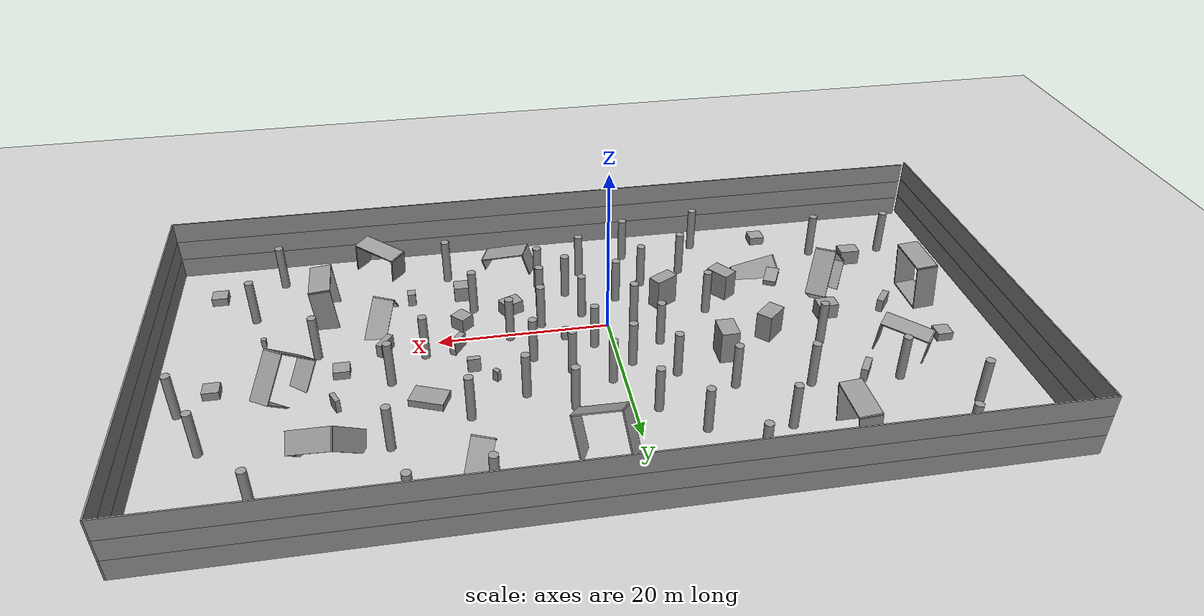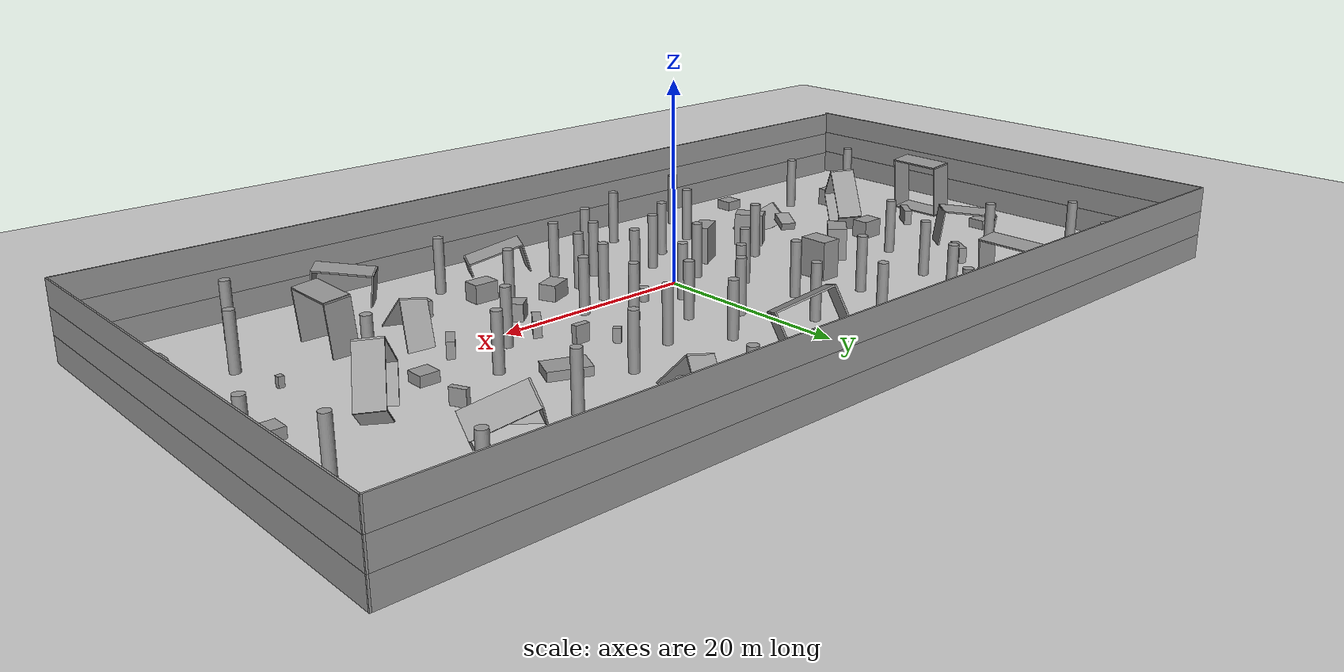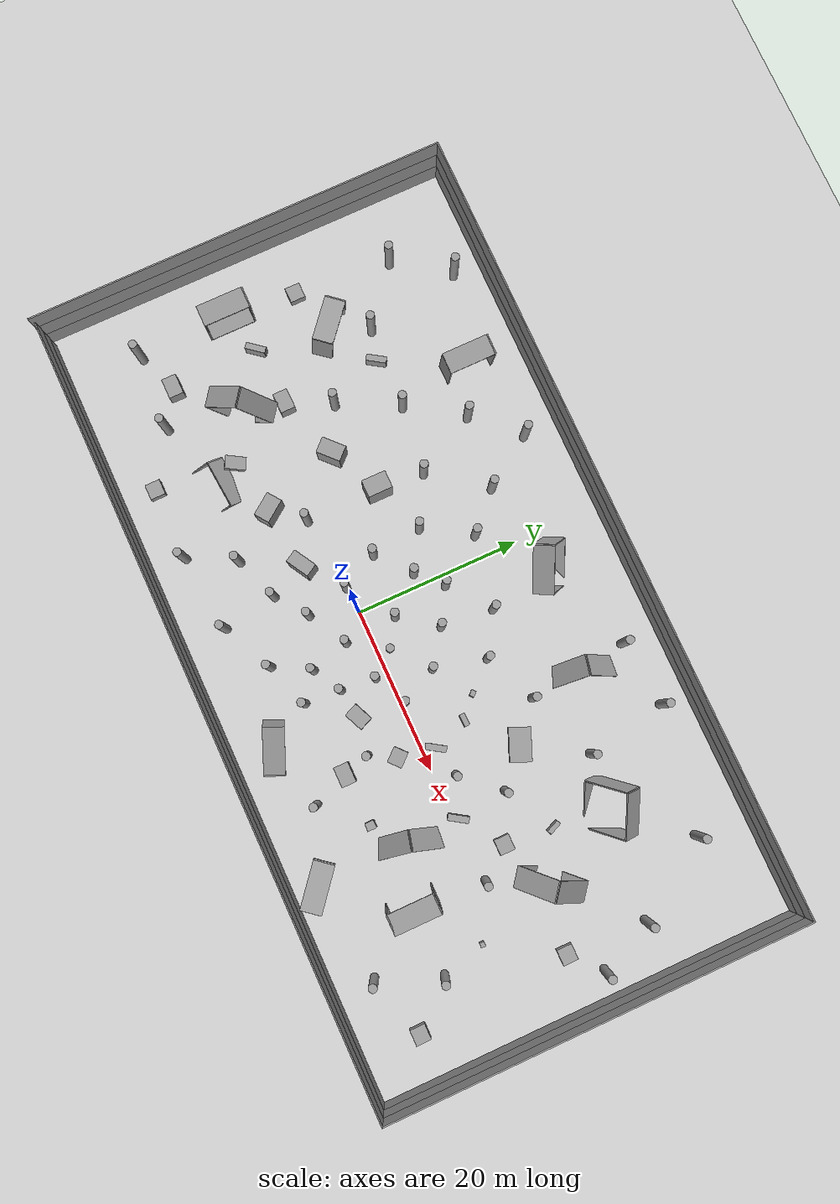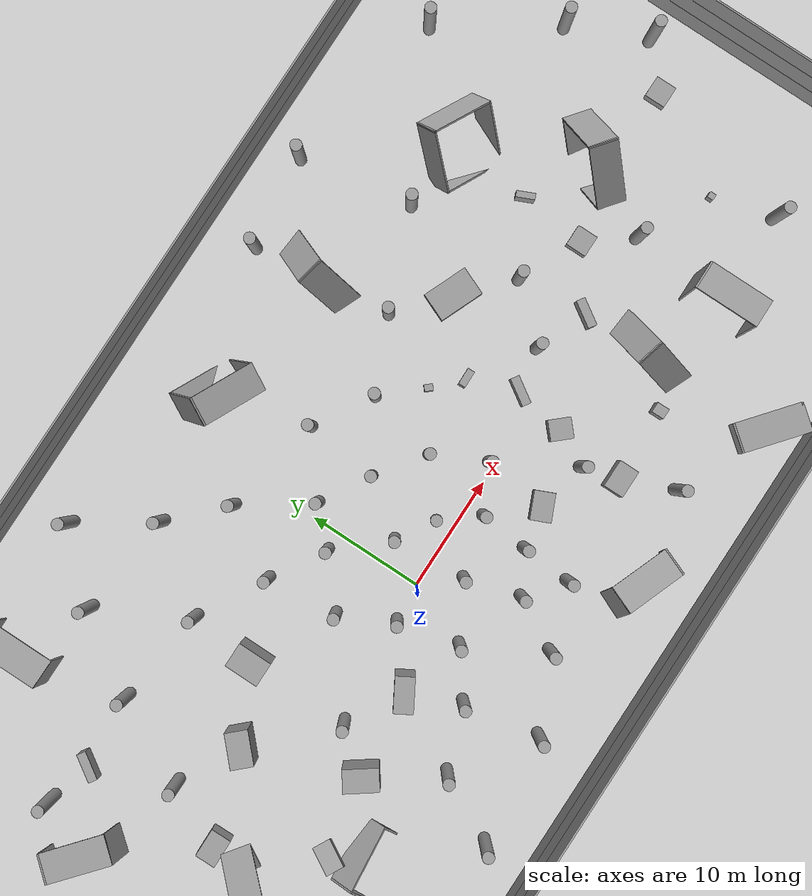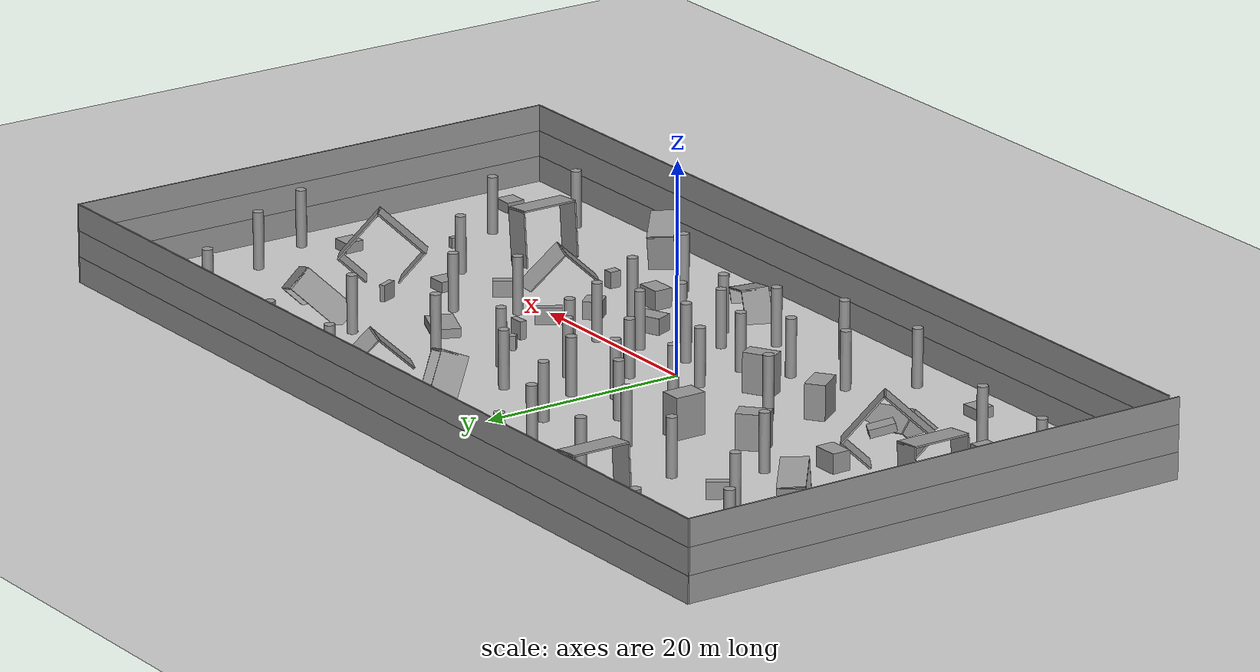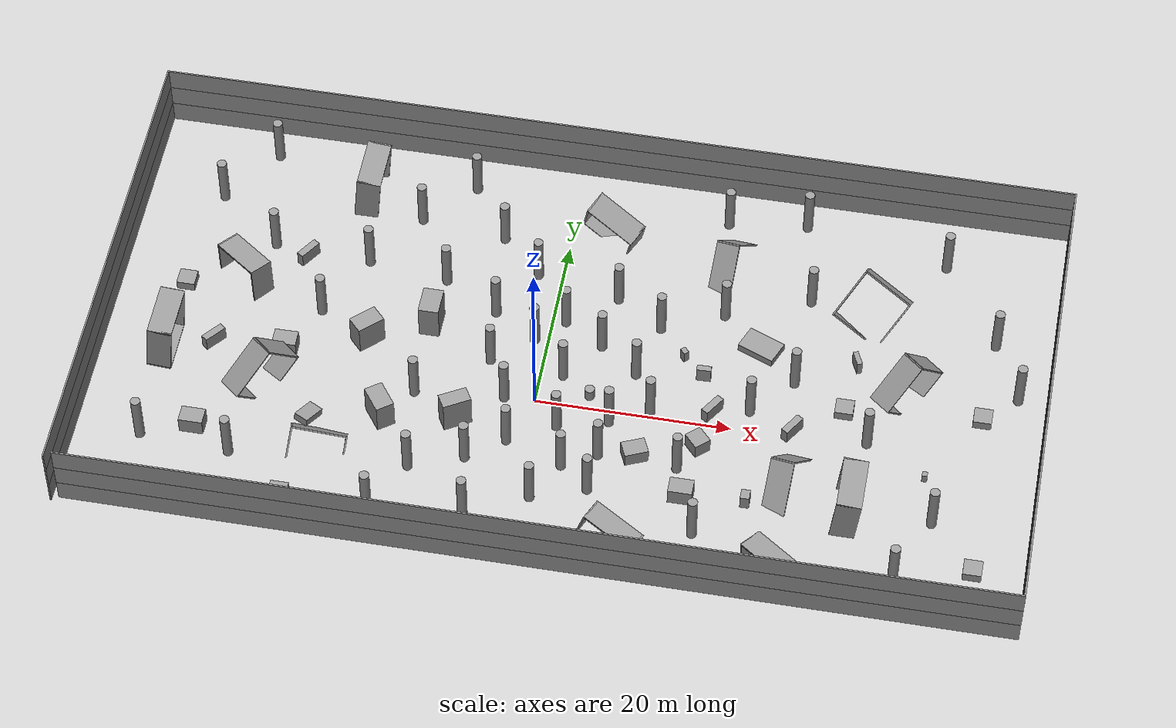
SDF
<sdf version="1.6">
 <world name="default">
  <light name="sun" type="directional">
   <pose>0 0 10 0 -0 0</pose>
   <diffuse>0.8 0.8 0.8 1</diffuse>
   <specular>0.2 0.2 0.2 1</specular>
   <attenuation>
    <range>1000</range>
    <constant>0.9</constant>
    <linear>0.01</linear>
    <quadratic>0.001</quadratic>
   </attenuation>
   <direction>-0.5 0.1 -0.9</direction>
  </light>
  <model name="ground_plane">
   <static>1</static>
   <link name="link">
    <collision name="collision">
     <geometry><plane><normal>0 0 1</normal><size>100 100</size></plane></geometry>
     <surface><friction><ode><mu>100</mu><mu2>50</mu2></ode></friction></surface>
    </collision>
    <visual name="visual">
     <cast_shadows>0</cast_shadows>
     <geometry><plane><normal>0 0 1</normal><size>100 100</size></plane></geometry>
     <material>
      <script><uri>file://media/materials/scripts/gazebo.material</uri><name>Gazebo/Grey</name></script>
     </material>
    </visual>
   </link>
  </model>
  <gravity>0 0 -9.8</gravity>
  <magnetic_field>6e-06 2.3e-05 -4.2e-05</magnetic_field>
  <atmosphere type="adiabatic"/>
  <physics name="default_physics" default="0" type="ode">
   <max_step_size>0.001</max_step_size>
   <real_time_factor>1</real_time_factor>
   <real_time_update_rate>1000</real_time_update_rate>
  </physics>
  <scene><ambient>0.4 0.4 0.4 1</ambient><background>0.7 0.7 0.7 1</background><shadows>1</shadows></scene>
  <audio><device>default</device></audio>
  <spherical_coordinates>
   <surface_model>EARTH_WGS84</surface_model>
   <latitude_deg>0</latitude_deg>
   <longitude_deg>0</longitude_deg>
   <elevation>0</elevation>
   <heading_deg>0</heading_deg>
  </spherical_coordinates>
  <model name="unit_cylinder">
   <pose>5.3177 1.52841 0.661765 0 -0 0.001729</pose>
   <link name="link">
    <inertial>
     <mass>1</mass>
     <inertia><ixx>0.145833</ixx><ixy>0</ixy><ixz>0</ixz><iyy>0.145833</iyy><iyz>0</iyz><izz>0.125</izz></inertia>
    </inertial>
    <collision name="collision">
     <geometry><cylinder><radius>0.5</radius><length>1.32353</length></cylinder></geometry>
    </collision>
    <visual name="visual">
     <geometry><cylinder><radius>0.5</radius><length>1.32353</length></cylinder></geometry>
     <material>
      <script><name>Gazebo/Grey</name><uri>file://media/materials/scripts/gazebo.material</uri></script>
     </material>
    </visual>
   </link>
  </model>
  <model name="unit_cylinder_clone">
   <pose>2.67985 -2.8047 2.75253 0 -0 0.004488</pose>
   <link name="link">
    <inertial>
     <mass>1</mass>
     <inertia><ixx>0.145833</ixx><ixy>0</ixy><ixz>0</ixz><iyy>0.145833</iyy><iyz>0</iyz><izz>0.125</izz></inertia>
    </inertial>
    <collision name="collision">
     <geometry><cylinder><radius>0.5</radius><length>5.50507</length></cylinder></geometry>
    </collision>
    <visual name="visual">
     <geometry><cylinder><radius>0.5</radius><length>5.50507</length></cylinder></geometry>
     <material>
      <script><name>Gazebo/Grey</name><uri>file://media/materials/scripts/gazebo.material</uri></script>
     </material>
    </visual>
   </link>
  </model>
  <model name="unit_cylinder_clone_0">
   <pose>2.22738 3.56207 2.75253 0 -0 0.003085</pose>
   <link name="link">
    <inertial>
     <mass>1</mass>
     <inertia><ixx>0.145833</ixx><ixy>0</ixy><ixz>0</ixz><iyy>0.145833</iyy><iyz>0</iyz><izz>0.125</izz></inertia>
    </inertial>
    <collision name="collision">
     <geometry><cylinder><radius>0.5</radius><length>5.50507</length></cylinder></geometry>
    </collision>
    <visual name="visual">
     <geometry><cylinder><radius>0.5</radius><length>5.50507</length></cylinder></geometry>
     <material>
      <script><name>Gazebo/Grey</name><uri>file://media/materials/scripts/gazebo.material</uri></script>
     </material>
    </visual>
   </link>
  </model>
  <model name="unit_cylinder_clone_1">
   <pose>7.38389 -5.59554 2.75253 0 -0 0.004343</pose>
   <link name="link">
    <inertial>
     <mass>1</mass>
     <inertia><ixx>0.145833</ixx><ixy>0</ixy><ixz>0</ixz><iyy>0.145833</iyy><iyz>0</iyz><izz>0.125</izz></inertia>
    </inertial>
    <collision name="collision">
     <geometry><cylinder><radius>0.5</radius><length>5.50507</length></cylinder></geometry>
    </collision>
    <visual name="visual">
     <geometry><cylinder><radius>0.5</radius><length>5.50507</length></cylinder></geometry>
     <material>
      <script><name>Gazebo/Grey</name><uri>file://media/materials/scripts/gazebo.material</uri></script>
     </material>
    </visual>
   </link>
  </model>
  <model name="unit_cylinder_clone_2">
   <pose>9.49308 5.0003 2.75253 0 -0 0.004498</pose>
   <link name="link">
    <inertial>
     <mass>1</mass>
     <inertia><ixx>0.145833</ixx><ixy>0</ixy><ixz>0</ixz><iyy>0.145833</iyy><iyz>0</iyz><izz>0.125</izz></inertia>
    </inertial>
    <collision name="collision">
     <geometry><cylinder><radius>0.5</radius><length>5.50507</length></cylinder></geometry>
    </collision>
    <visual name="visual">
     <geometry><cylinder><radius>0.5</radius><length>5.50507</length></cylinder></geometry>
     <material>
      <script><name>Gazebo/Grey</name><uri>file://media/materials/scripts/gazebo.material</uri></script>
     </material>
    </visual>
   </link>
  </model>
  <model name="unit_cylinder_clone_3">
   <pose>7.77783 -1.37946 2.75253 0 -0 0.00474</pose>
   <link name="link">
    <inertial>
     <mass>1</mass>
     <inertia><ixx>0.145833</ixx><ixy>0</ixy><ixz>0</ixz><iyy>0.145833</iyy><iyz>0</iyz><izz>0.125</izz></inertia>
    </inertial>
    <collision name="collision">
     <geometry><cylinder><radius>0.5</radius><length>5.50507</length></cylinder></geometry>
    </collision>
    <visual name="visual">
     <geometry><cylinder><radius>0.5</radius><length>5.50507</length></cylinder></geometry>
     <material>
      <script><name>Gazebo/Grey</name><uri>file://media/materials/scripts/gazebo.material</uri></script>
     </material>
    </visual>
   </link>
  </model>
  <model name="unit_cylinder_clone_4">
   <pose>3.98651 -7.52504 2.75253 0 -0 0.004053</pose>
   <link name="link">
    <inertial>
     <mass>1</mass>
     <inertia><ixx>0.145833</ixx><ixy>0</ixy><ixz>0</ixz><iyy>0.145833</iyy><iyz>0</iyz><izz>0.125</izz></inertia>
    </inertial>
    <collision name="collision">
     <geometry><cylinder><radius>0.5</radius><length>5.50507</length></cylinder></geometry>
    </collision>
    <visual name="visual">
     <geometry><cylinder><radius>0.5</radius><length>5.50507</length></cylinder></geometry>
     <material>
      <script><name>Gazebo/Grey</name><uri>file://media/materials/scripts/gazebo.material</uri></script>
     </material>
    </visual>
   </link>
  </model>
  <model name="unit_cylinder_clone_5">
   <pose>5.48129 7.9192 2.75253 0 -0 0.004331</pose>
   <link name="link">
    <inertial>
     <mass>1</mass>
     <inertia><ixx>0.145833</ixx><ixy>0</ixy><ixz>0</ixz><iyy>0.145833</iyy><iyz>0</iyz><izz>0.125</izz></inertia>
    </inertial>
    <collision name="collision">
     <geometry><cylinder><radius>0.5</radius><length>5.50507</length></cylinder></geometry>
    </collision>
    <visual name="visual">
     <geometry><cylinder><radius>0.5</radius><length>5.50507</length></cylinder></geometry>
     <material>
      <script><name>Gazebo/Grey</name><uri>file://media/materials/scripts/gazebo.material</uri></script>
     </material>
    </visual>
   </link>
  </model>
  <model name="unit_cylinder_clone_6">
   <pose>7.07349 -9.96307 2.75253 0 -0 0.004298</pose>
   <link name="link">
    <inertial>
     <mass>1</mass>
     <inertia><ixx>0.145833</ixx><ixy>0</ixy><ixz>0</ixz><iyy>0.145833</iyy><iyz>0</iyz><izz>0.125</izz></inertia>
    </inertial>
    <collision name="collision">
     <geometry><cylinder><radius>0.5</radius><length>5.50507</length></cylinder></geometry>
    </collision>
    <visual name="visual">
     <geometry><cylinder><radius>0.5</radius><length>5.50507</length></cylinder></geometry>
     <material>
      <script><name>Gazebo/Grey</name><uri>file://media/materials/scripts/gazebo.material</uri></script>
     </material>
    </visual>
   </link>
  </model>
  <model name="unit_cylinder_clone_7">
   <pose>11.6635 0.575261 2.75253 0 -0 0.004485</pose>
   <link name="link">
    <inertial>
     <mass>1</mass>
     <inertia><ixx>0.145833</ixx><ixy>0</ixy><ixz>0</ixz><iyy>0.145833</iyy><iyz>0</iyz><izz>0.125</izz></inertia>
    </inertial>
    <collision name="collision">
     <geometry><cylinder><radius>0.5</radius><length>5.50507</length></cylinder></geometry>
    </collision>
    <visual name="visual">
     <geometry><cylinder><radius>0.5</radius><length>5.50507</length></cylinder></geometry>
     <material>
      <script><name>Gazebo/Grey</name><uri>file://media/materials/scripts/gazebo.material</uri></script>
     </material>
    </visual>
   </link>
  </model>
  <model name="unit_cylinder_clone_8">
   <pose>11.0383 11.2509 2.75253 0 -0 0.004416</pose>
   <link name="link">
    <inertial>
     <mass>1</mass>
     <inertia><ixx>0.145833</ixx><ixy>0</ixy><ixz>0</ixz><iyy>0.145833</iyy><iyz>0</iyz><izz>0.125</izz></inertia>
    </inertial>
    <collision name="collision">
     <geometry><cylinder><radius>0.5</radius><length>5.50507</length></cylinder></geometry>
    </collision>
    <visual name="visual">
     <geometry><cylinder><radius>0.5</radius><length>5.50507</length></cylinder></geometry>
     <material>
      <script><name>Gazebo/Grey</name><uri>file://media/materials/scripts/gazebo.material</uri></script>
     </material>
    </visual>
   </link>
  </model>
  <model name="unit_cylinder_clone_9">
   <pose>1.3235 10.3758 2.75253 0 -0 0.004596</pose>
   <link name="link">
    <inertial>
     <mass>1</mass>
     <inertia><ixx>0.145833</ixx><ixy>0</ixy><ixz>0</ixz><iyy>0.145833</iyy><iyz>0</iyz><izz>0.125</izz></inertia>
    </inertial>
    <collision name="collision">
     <geometry><cylinder><radius>0.5</radius><length>5.50507</length></cylinder></geometry>
    </collision>
    <visual name="visual">
     <geometry><cylinder><radius>0.5</radius><length>5.50507</length></cylinder></geometry>
     <material>
      <script><name>Gazebo/Grey</name><uri>file://media/materials/scripts/gazebo.material</uri></script>
     </material>
    </visual>
   </link>
  </model>
  <model name="unit_cylinder_clone_12">
   <pose>15.4123 -5.85656 2.75253 0 -0 0.004745</pose>
   <link name="link">
    <inertial>
     <mass>1</mass>
     <inertia><ixx>0.145833</ixx><ixy>0</ixy><ixz>0</ixz><iyy>0.145833</iyy><iyz>0</iyz><izz>0.125</izz></inertia>
    </inertial>
    <collision name="collision">
     <geometry><cylinder><radius>0.5</radius><length>5.50507</length></cylinder></geometry>
    </collision>
    <visual name="visual">
     <geometry><cylinder><radius>0.5</radius><length>5.50507</length></cylinder></geometry>
     <material>
      <script><name>Gazebo/Grey</name><uri>file://media/materials/scripts/gazebo.material</uri></script>
     </material>
    </visual>
   </link>
  </model>
  <model name="unit_box">
   <pose>13.9889 7.99618 0.67243 1e-06 -0 0.739122</pose>
   <link name="link">
    <inertial>
     <mass>1</mass>
     <inertia>
      <ixx>0.166667</ixx>
      <ixy>0</ixy>
      <ixz>0</ixz>
      <iyy>0.166667</iyy>
      <iyz>0</iyz>
      <izz>0.166667</izz>
     </inertia>
    </inertial>
    <collision name="collision"><geometry><box><size>0.564982 0.726007 1.34486</size></box></geometry></collision>
    <visual name="visual">
     <geometry><box><size>0.564982 0.726007 1.34486</size></box></geometry>
     <material>
      <script><name>Gazebo/Grey</name><uri>file://media/materials/scripts/gazebo.material</uri></script>
     </material>
    </visual>
   </link>
  </model>
  <model name="unit_box_clone">
   <pose>11 -5.00016 0.78823 -4e-06 0 -1.1578</pose>
   <link name="link">
    <inertial>
     <mass>1</mass>
     <inertia>
      <ixx>0.166667</ixx>
      <ixy>0</ixy>
      <ixz>0</ixz>
      <iyy>0.166667</iyy>
      <iyz>0</iyz>
      <izz>0.166667</izz>
     </inertia>
    </inertial>
    <collision name="collision"><geometry><box><size>1.76997 2.44518 1.57647</size></box></geometry></collision>
    <visual name="visual">
     <geometry><box><size>1.76997 2.44518 1.57647</size></box></geometry>
     <material>
      <script><name>Gazebo/Grey</name><uri>file://media/materials/scripts/gazebo.material</uri></script>
     </material>
    </visual>
   </link>
  </model>
  <model name="unit_box_clone_0">
   <pose>17.0265 -2.7958 0.841035 -5e-06 -0 0.728675</pose>
   <link name="link">
    <inertial>
     <mass>1</mass>
     <inertia>
      <ixx>0.166667</ixx>
      <ixy>0</ixy>
      <ixz>0</ixz>
      <iyy>0.166667</iyy>
      <iyz>0</iyz>
      <izz>0.166667</izz>
     </inertia>
    </inertial>
    <collision name="collision"><geometry><box><size>1.76997 1.92154 1.68208</size></box></geometry></collision>
    <visual name="visual">
     <geometry><box><size>1.76997 1.92154 1.68208</size></box></geometry>
     <material>
      <script><name>Gazebo/Grey</name><uri>file://media/materials/scripts/gazebo.material</uri></script>
     </material>
    </visual>
   </link>
  </model>
  <model name="unit_box_clone_1">
   <pose>16.3355 -9.0602 0.926305 0 -0 1.57085</pose>
   <link name="link">
    <inertial>
     <mass>1</mass>
     <inertia>
      <ixx>0.166667</ixx>
      <ixy>0</ixy>
      <ixz>0</ixz>
      <iyy>0.166667</iyy>
      <iyz>0</iyz>
      <izz>0.166667</izz>
     </inertia>
    </inertial>
    <collision name="collision"><geometry><box><size>1.76997 2.44518 1.85261</size></box></geometry></collision>
    <visual name="visual">
     <geometry><box><size>1.76997 2.44518 1.85261</size></box></geometry>
     <material>
      <script><name>Gazebo/Grey</name><uri>file://media/materials/scripts/gazebo.material</uri></script>
     </material>
    </visual>
   </link>
  </model>
  <model name="unit_box_clone_0_clone">
   <pose>21.5162 10.5077 0.430373 1.55805 -1.57079 -1.95161</pose>
   <link name="link">
    <inertial>
     <mass>1</mass>
     <inertia>
      <ixx>0.166667</ixx>
      <ixy>0</ixy>
      <ixz>0</ixz>
      <iyy>0.166667</iyy>
      <iyz>0</iyz>
      <izz>0.166667</izz>
     </inertia>
    </inertial>
    <collision name="collision"><geometry><box><size>0.860775 2.57296 3.98743</size></box></geometry></collision>
    <visual name="visual">
     <geometry><box><size>0.860775 2.57296 3.98743</size></box></geometry>
     <material>
      <script><name>Gazebo/Grey</name><uri>file://media/materials/scripts/gazebo.material</uri></script>
     </material>
    </visual>
   </link>
  </model>
  <model name="unit_box_0">
   <pose>16.3175 5.84891 0.859719 0 7e-06 0.022308</pose>
   <link name="link">
    <inertial>
     <mass>1</mass>
     <inertia>
      <ixx>0.166667</ixx>
      <ixy>0</ixy>
      <ixz>0</ixz>
      <iyy>0.166667</iyy>
      <iyz>0</iyz>
      <izz>0.166667</izz>
     </inertia>
    </inertial>
    <collision name="collision"><geometry><box><size>1.47389 0.631413 1.71945</size></box></geometry></collision>
    <visual name="visual">
     <geometry><box><size>1.47389 0.631413 1.71945</size></box></geometry>
     <material>
      <script><name>Gazebo/Grey</name><uri>file://media/materials/scripts/gazebo.material</uri></script>
     </material>
    </visual>
   </link>
  </model>
  <model name="unit_box_clone_clone">
   <pose>26.0947 0.596068 0.788231 -4e-06 -0 -0.576118</pose>
   <link name="link">
    <inertial>
     <mass>1</mass>
     <inertia>
      <ixx>0.166667</ixx>
      <ixy>0</ixy>
      <ixz>0</ixz>
      <iyy>0.166667</iyy>
      <iyz>0</iyz>
      <izz>0.166667</izz>
     </inertia>
    </inertial>
    <collision name="collision"><geometry><box><size>0.770315 2.44518 1.57647</size></box></geometry></collision>
    <visual name="visual">
     <geometry><box><size>0.770315 2.44518 1.57647</size></box></geometry>
     <material>
      <script><name>Gazebo/Grey</name><uri>file://media/materials/scripts/gazebo.material</uri></script>
     </material>
    </visual>
   </link>
  </model>
  <model name="unit_box_clone_clone_0">
   <pose>22.7327 -8.74636 0.788235 0 -0 0.001396</pose>
   <link name="link">
    <inertial>
     <mass>1</mass>
     <inertia>
      <ixx>0.166667</ixx>
      <ixy>0</ixy>
      <ixz>0</ixz>
      <iyy>0.166667</iyy>
      <iyz>0</iyz>
      <izz>0.166667</izz>
     </inertia>
    </inertial>
    <collision name="collision"><geometry><box><size>0.926366 1.10204 1.57647</size></box></geometry></collision>
    <visual name="visual">
     <geometry><box><size>0.926366 1.10204 1.57647</size></box></geometry>
     <material>
      <script><name>Gazebo/Grey</name><uri>file://media/materials/scripts/gazebo.material</uri></script>
     </material>
    </visual>
   </link>
  </model>
  <model name="unit_box_clone_clone_1">
   <pose>31.4556 9.98516 0.788235 -0 -0 -2.72542</pose>
   <link name="link">
    <inertial>
     <mass>1</mass>
     <inertia>
      <ixx>0.166667</ixx>
      <ixy>0</ixy>
      <ixz>0</ixz>
      <iyy>0.166667</iyy>
      <iyz>0</iyz>
      <izz>0.166667</izz>
     </inertia>
    </inertial>
    <collision name="collision"><geometry><box><size>0.539862 1.60938 1.57647</size></box></geometry></collision>
    <visual name="visual">
     <geometry><box><size>0.539862 1.60938 1.57647</size></box></geometry>
     <material>
      <script><name>Gazebo/Grey</name><uri>file://media/materials/scripts/gazebo.material</uri></script>
     </material>
    </visual>
   </link>
  </model>
  <model name="unit_cylinder_clone_7_clone_0">
   <pose>25.5021 6.72855 2.75253 0 -0 0.004488</pose>
   <link name="link">
    <inertial>
     <mass>1</mass>
     <inertia><ixx>0.145833</ixx><ixy>0</ixy><ixz>0</ixz><iyy>0.145833</iyy><iyz>0</iyz><izz>0.125</izz></inertia>
    </inertial>
    <collision name="collision">
     <geometry><cylinder><radius>0.5</radius><length>5.50507</length></cylinder></geometry>
    </collision>
    <visual name="visual">
     <geometry><cylinder><radius>0.5</radius><length>5.50507</length></cylinder></geometry>
     <material>
      <script><name>Gazebo/Grey</name><uri>file://media/materials/scripts/gazebo.material</uri></script>
     </material>
    </visual>
   </link>
  </model>
  <model name="unit_cylinder_clone_7_clone_1">
   <pose>21.564 2.39876 2.75253 0 -0 0.006125</pose>
   <link name="link">
    <inertial>
     <mass>1</mass>
     <inertia><ixx>0.145833</ixx><ixy>0</ixy><ixz>0</ixz><iyy>0.145833</iyy><iyz>0</iyz><izz>0.125</izz></inertia>
    </inertial>
    <collision name="collision">
     <geometry><cylinder><radius>0.5</radius><length>5.50507</length></cylinder></geometry>
    </collision>
    <visual name="visual">
     <geometry><cylinder><radius>0.5</radius><length>5.50507</length></cylinder></geometry>
     <material>
      <script><name>Gazebo/Grey</name><uri>file://media/materials/scripts/gazebo.material</uri></script>
     </material>
    </visual>
   </link>
  </model>
  <model name="unit_cylinder_clone_7_clone_2">
   <pose>17.2791 14.0466 2.75253 0 -0 0.00434</pose>
   <link name="link">
    <inertial>
     <mass>1</mass>
     <inertia><ixx>0.145833</ixx><ixy>0</ixy><ixz>0</ixz><iyy>0.145833</iyy><iyz>0</iyz><izz>0.125</izz></inertia>
    </inertial>
    <collision name="collision">
     <geometry><cylinder><radius>0.5</radius><length>5.50507</length></cylinder></geometry>
    </collision>
    <visual name="visual">
     <geometry><cylinder><radius>0.5</radius><length>5.50507</length></cylinder></geometry>
     <material>
      <script><name>Gazebo/Grey</name><uri>file://media/materials/scripts/gazebo.material</uri></script>
     </material>
    </visual>
   </link>
  </model>
  <model name="unit_cylinder_clone_7_clone_3">
   <pose>18.1053 -13.3671 2.75253 0 -0 0.004413</pose>
   <link name="link">
    <inertial>
     <mass>1</mass>
     <inertia><ixx>0.145833</ixx><ixy>0</ixy><ixz>0</ixz><iyy>0.145833</iyy><iyz>0</iyz><izz>0.125</izz></inertia>
    </inertial>
    <collision name="collision">
     <geometry><cylinder><radius>0.5</radius><length>5.50507</length></cylinder></geometry>
    </collision>
    <visual name="visual">
     <geometry><cylinder><radius>0.5</radius><length>5.50507</length></cylinder></geometry>
     <material>
      <script><name>Gazebo/Grey</name><uri>file://media/materials/scripts/gazebo.material</uri></script>
     </material>
    </visual>
   </link>
  </model>
  <model name="vRoom_clone_3_clone_clone_9">
   <link name="Wall_0">
    <pose>-2.8 -0 -1e-06 -0 -0 -1.5708</pose>
    <velocity_decay><linear>0</linear><angular>0</angular></velocity_decay>
    <visual name="Wall_0_Visual">
     <pose>0 0 1.25 0 -0 0</pose>
     <geometry><box><size>5.75 0.15 2.5</size></box></geometry>
     <material>
      <script><uri>file://media/materials/scripts/gazebo.material</uri><name>Gazebo/Grey</name></script>
      <ambient>1 1 1 1</ambient>
     </material>
    </visual>
    <collision name="Wall_0_Collision">
     <pose>0 0 1.25 0 -0 0</pose>
     <geometry><box><size>5.75 0.15 2.5</size></box></geometry>
     <surface>
      <friction>
       <ode><mu>1</mu><mu2>1</mu2><fdir1>0 0 0</fdir1><slip1>0</slip1><slip2>0</slip2></ode>
       <torsional>
        <coefficient>1</coefficient>
        <patch_radius>0</patch_radius>
        <surface_radius>0</surface_radius>
        <use_patch_radius>1</use_patch_radius>
        <ode><slip>0</slip></ode>
       </torsional>
      </friction>
      <bounce><restitution_coefficient>0</restitution_coefficient><threshold>1e+06</threshold></bounce>
      <contact>
       <collide_without_contact>0</collide_without_contact>
       <collide_without_contact_bitmask>1</collide_without_contact_bitmask>
       <collide_bitmask>1</collide_bitmask>
       <ode>
        <soft_cfm>0</soft_cfm>
        <soft_erp>0.2</soft_erp>
        <kp>1e+13</kp>
        <kd>1</kd>
        <max_vel>0.01</max_vel>
        <min_depth>0</min_depth>
       </ode>
       <bullet>
        <split_impulse>1</split_impulse>
        <split_impulse_penetration_threshold>-0.01</split_impulse_penetration_threshold>
        <soft_cfm>0</soft_cfm>
        <soft_erp>0.2</soft_erp>
        <kp>1e+13</kp>
        <kd>1</kd>
       </bullet>
      </contact>
     </surface>
    </collision>
   </link>
   <link name="Wall_1">
    <pose>2e-06 -2.8 2e-06 0 -0 0</pose>
    <velocity_decay><linear>0</linear><angular>0</angular></velocity_decay>
    <visual name="Wall_1_Visual">
     <pose>0 0 1.25 0 -0 0</pose>
     <geometry><box><size>5.75 0.15 2.5</size></box></geometry>
     <material>
      <script><uri>file://media/materials/scripts/gazebo.material</uri><name>Gazebo/Grey</name></script>
      <ambient>1 1 1 1</ambient>
     </material>
    </visual>
    <collision name="Wall_1_Collision">
     <pose>0 0 1.25 0 -0 0</pose>
     <geometry><box><size>5.75 0.15 2.5</size></box></geometry>
     <surface>
      <friction>
       <ode><mu>1</mu><mu2>1</mu2><fdir1>0 0 0</fdir1><slip1>0</slip1><slip2>0</slip2></ode>
       <torsional>
        <coefficient>1</coefficient>
        <patch_radius>0</patch_radius>
        <surface_radius>0</surface_radius>
        <use_patch_radius>1</use_patch_radius>
        <ode><slip>0</slip></ode>
       </torsional>
      </friction>
      <bounce><restitution_coefficient>0</restitution_coefficient><threshold>1e+06</threshold></bounce>
      <contact>
       <collide_without_contact>0</collide_without_contact>
       <collide_without_contact_bitmask>1</collide_without_contact_bitmask>
       <collide_bitmask>1</collide_bitmask>
       <ode>
        <soft_cfm>0</soft_cfm>
        <soft_erp>0.2</soft_erp>
        <kp>1e+13</kp>
        <kd>1</kd>
        <max_vel>0.01</max_vel>
        <min_depth>0</min_depth>
       </ode>
       <bullet>
        <split_impulse>1</split_impulse>
        <split_impulse_penetration_threshold>-0.01</split_impulse_penetration_threshold>
        <soft_cfm>0</soft_cfm>
        <soft_erp>0.2</soft_erp>
        <kp>1e+13</kp>
        <kd>1</kd>
       </bullet>
      </contact>
     </surface>
    </collision>
   </link>
   <link name="Wall_2">
    <pose>2.8 0 1e-06 0 -0 1.5708</pose>
    <velocity_decay><linear>0</linear><angular>0</angular></velocity_decay>
    <visual name="Wall_2_Visual">
     <pose>0 0 1.25 0 -0 0</pose>
     <geometry><box><size>5.75 0.15 2.5</size></box></geometry>
     <material>
      <script><uri>file://media/materials/scripts/gazebo.material</uri><name>Gazebo/Grey</name></script>
      <ambient>1 1 1 1</ambient>
     </material>
    </visual>
    <collision name="Wall_2_Collision">
     <pose>0 0 1.25 0 -0 0</pose>
     <geometry><box><size>5.75 0.15 2.5</size></box></geometry>
     <surface>
      <friction>
       <ode><mu>1</mu><mu2>1</mu2><fdir1>0 0 0</fdir1><slip1>0</slip1><slip2>0</slip2></ode>
       <torsional>
        <coefficient>1</coefficient>
        <patch_radius>0</patch_radius>
        <surface_radius>0</surface_radius>
        <use_patch_radius>1</use_patch_radius>
        <ode><slip>0</slip></ode>
       </torsional>
      </friction>
      <bounce><restitution_coefficient>0</restitution_coefficient><threshold>1e+06</threshold></bounce>
      <contact>
       <collide_without_contact>0</collide_without_contact>
       <collide_without_contact_bitmask>1</collide_without_contact_bitmask>
       <collide_bitmask>1</collide_bitmask>
       <ode>
        <soft_cfm>0</soft_cfm>
        <soft_erp>0.2</soft_erp>
        <kp>1e+13</kp>
        <kd>1</kd>
        <max_vel>0.01</max_vel>
        <min_depth>0</min_depth>
       </ode>
       <bullet>
        <split_impulse>1</split_impulse>
        <split_impulse_penetration_threshold>-0.01</split_impulse_penetration_threshold>
        <soft_cfm>0</soft_cfm>
        <soft_erp>0.2</soft_erp>
        <kp>1e+13</kp>
        <kd>1</kd>
       </bullet>
      </contact>
     </surface>
    </collision>
   </link>
   <link name="Wall_3">
    <pose>-2e-06 2.8 -2e-06 0 -0 3.14159</pose>
    <velocity_decay><linear>0</linear><angular>0</angular></velocity_decay>
    <visual name="Wall_3_Visual">
     <pose>0 0 1.25 0 -0 0</pose>
     <geometry><box><size>5.75 0.15 2.5</size></box></geometry>
     <material>
      <script><uri>file://media/materials/scripts/gazebo.material</uri><name>Gazebo/Grey</name></script>
      <ambient>1 1 1 1</ambient>
     </material>
    </visual>
    <collision name="Wall_3_Collision">
     <pose>0 0 1.25 0 -0 0</pose>
     <geometry><box><size>5.75 0.15 2.5</size></box></geometry>
     <surface>
      <friction>
       <ode><mu>1</mu><mu2>1</mu2><fdir1>0 0 0</fdir1><slip1>0</slip1><slip2>0</slip2></ode>
       <torsional>
        <coefficient>1</coefficient>
        <patch_radius>0</patch_radius>
        <surface_radius>0</surface_radius>
        <use_patch_radius>1</use_patch_radius>
        <ode><slip>0</slip></ode>
       </torsional>
      </friction>
      <bounce><restitution_coefficient>0</restitution_coefficient><threshold>1e+06</threshold></bounce>
      <contact>
       <collide_without_contact>0</collide_without_contact>
       <collide_without_contact_bitmask>1</collide_without_contact_bitmask>
       <collide_bitmask>1</collide_bitmask>
       <ode>
        <soft_cfm>0</soft_cfm>
        <soft_erp>0.2</soft_erp>
        <kp>1e+13</kp>
        <kd>1</kd>
        <max_vel>0.01</max_vel>
        <min_depth>0</min_depth>
       </ode>
       <bullet>
        <split_impulse>1</split_impulse>
        <split_impulse_penetration_threshold>-0.01</split_impulse_penetration_threshold>
        <soft_cfm>0</soft_cfm>
        <soft_erp>0.2</soft_erp>
        <kp>1e+13</kp>
        <kd>1</kd>
       </bullet>
      </contact>
     </surface>
    </collision>
   </link>
   <static>1</static>
   <pose>34.1246 -8.07118 2.16038 4e-06 -1.47998 -7e-06</pose>
  </model>
  <model name="vRoom_clone_3_clone_clone_9_clone">
   <link name="Wall_0">
    <pose>-2.8 -0 -1e-06 -0 -0 -1.5708</pose>
    <velocity_decay><linear>0</linear><angular>0</angular></velocity_decay>
    <visual name="Wall_0_Visual">
     <pose>0 0 1.25 0 -0 0</pose>
     <geometry><box><size>5.75 0.15 2.5</size></box></geometry>
     <material>
      <script><uri>file://media/materials/scripts/gazebo.material</uri><name>Gazebo/Grey</name></script>
      <ambient>1 1 1 1</ambient>
     </material>
    </visual>
    <collision name="Wall_0_Collision">
     <pose>0 0 1.25 0 -0 0</pose>
     <geometry><box><size>5.75 0.15 2.5</size></box></geometry>
     <surface>
      <friction>
       <ode><mu>1</mu><mu2>1</mu2><fdir1>0 0 0</fdir1><slip1>0</slip1><slip2>0</slip2></ode>
       <torsional>
        <coefficient>1</coefficient>
        <patch_radius>0</patch_radius>
        <surface_radius>0</surface_radius>
        <use_patch_radius>1</use_patch_radius>
        <ode><slip>0</slip></ode>
       </torsional>
      </friction>
      <bounce><restitution_coefficient>0</restitution_coefficient><threshold>1e+06</threshold></bounce>
      <contact>
       <collide_without_contact>0</collide_without_contact>
       <collide_without_contact_bitmask>1</collide_without_contact_bitmask>
       <collide_bitmask>1</collide_bitmask>
       <ode>
        <soft_cfm>0</soft_cfm>
        <soft_erp>0.2</soft_erp>
        <kp>1e+13</kp>
        <kd>1</kd>
        <max_vel>0.01</max_vel>
        <min_depth>0</min_depth>
       </ode>
       <bullet>
        <split_impulse>1</split_impulse>
        <split_impulse_penetration_threshold>-0.01</split_impulse_penetration_threshold>
        <soft_cfm>0</soft_cfm>
        <soft_erp>0.2</soft_erp>
        <kp>1e+13</kp>
        <kd>1</kd>
       </bullet>
      </contact>
     </surface>
    </collision>
   </link>
   <link name="Wall_1">
    <pose>2e-06 -2.8 2e-06 0 -0 0</pose>
    <velocity_decay><linear>0</linear><angular>0</angular></velocity_decay>
    <visual name="Wall_1_Visual">
     <pose>0 0 1.25 0 -0 0</pose>
     <geometry><box><size>5.75 0.15 2.5</size></box></geometry>
     <material>
      <script><uri>file://media/materials/scripts/gazebo.material</uri><name>Gazebo/Grey</name></script>
      <ambient>1 1 1 1</ambient>
     </material>
    </visual>
    <collision name="Wall_1_Collision">
     <pose>0 0 1.25 0 -0 0</pose>
     <geometry><box><size>5.75 0.15 2.5</size></box></geometry>
     <surface>
      <friction>
       <ode><mu>1</mu><mu2>1</mu2><fdir1>0 0 0</fdir1><slip1>0</slip1><slip2>0</slip2></ode>
       <torsional>
        <coefficient>1</coefficient>
        <patch_radius>0</patch_radius>
        <surface_radius>0</surface_radius>
        <use_patch_radius>1</use_patch_radius>
        <ode><slip>0</slip></ode>
       </torsional>
      </friction>
      <bounce><restitution_coefficient>0</restitution_coefficient><threshold>1e+06</threshold></bounce>
      <contact>
       <collide_without_contact>0</collide_without_contact>
       <collide_without_contact_bitmask>1</collide_without_contact_bitmask>
       <collide_bitmask>1</collide_bitmask>
       <ode>
        <soft_cfm>0</soft_cfm>
        <soft_erp>0.2</soft_erp>
        <kp>1e+13</kp>
        <kd>1</kd>
        <max_vel>0.01</max_vel>
        <min_depth>0</min_depth>
       </ode>
       <bullet>
        <split_impulse>1</split_impulse>
        <split_impulse_penetration_threshold>-0.01</split_impulse_penetration_threshold>
        <soft_cfm>0</soft_cfm>
        <soft_erp>0.2</soft_erp>
        <kp>1e+13</kp>
        <kd>1</kd>
       </bullet>
      </contact>
     </surface>
    </collision>
   </link>
   <link name="Wall_2">
    <pose>2.8 0 1e-06 0 -0 1.5708</pose>
    <velocity_decay><linear>0</linear><angular>0</angular></velocity_decay>
    <visual name="Wall_2_Visual">
     <pose>0 0 1.25 0 -0 0</pose>
     <geometry><box><size>5.75 0.15 2.5</size></box></geometry>
     <material>
      <script><uri>file://media/materials/scripts/gazebo.material</uri><name>Gazebo/Grey</name></script>
      <ambient>1 1 1 1</ambient>
     </material>
    </visual>
    <collision name="Wall_2_Collision">
     <pose>0 0 1.25 0 -0 0</pose>
     <geometry><box><size>5.75 0.15 2.5</size></box></geometry>
     <surface>
      <friction>
       <ode><mu>1</mu><mu2>1</mu2><fdir1>0 0 0</fdir1><slip1>0</slip1><slip2>0</slip2></ode>
       <torsional>
        <coefficient>1</coefficient>
        <patch_radius>0</patch_radius>
        <surface_radius>0</surface_radius>
        <use_patch_radius>1</use_patch_radius>
        <ode><slip>0</slip></ode>
       </torsional>
      </friction>
      <bounce><restitution_coefficient>0</restitution_coefficient><threshold>1e+06</threshold></bounce>
      <contact>
       <collide_without_contact>0</collide_without_contact>
       <collide_without_contact_bitmask>1</collide_without_contact_bitmask>
       <collide_bitmask>1</collide_bitmask>
       <ode>
        <soft_cfm>0</soft_cfm>
        <soft_erp>0.2</soft_erp>
        <kp>1e+13</kp>
        <kd>1</kd>
        <max_vel>0.01</max_vel>
        <min_depth>0</min_depth>
       </ode>
       <bullet>
        <split_impulse>1</split_impulse>
        <split_impulse_penetration_threshold>-0.01</split_impulse_penetration_threshold>
        <soft_cfm>0</soft_cfm>
        <soft_erp>0.2</soft_erp>
        <kp>1e+13</kp>
        <kd>1</kd>
       </bullet>
      </contact>
     </surface>
    </collision>
   </link>
   <link name="Wall_3">
    <pose>-2e-06 2.8 -2e-06 0 -0 3.14159</pose>
    <velocity_decay><linear>0</linear><angular>0</angular></velocity_decay>
    <visual name="Wall_3_Visual">
     <pose>0 0 1.25 0 -0 0</pose>
     <geometry><box><size>5.75 0.15 2.5</size></box></geometry>
     <material>
      <script><uri>file://media/materials/scripts/gazebo.material</uri><name>Gazebo/Grey</name></script>
      <ambient>1 1 1 1</ambient>
     </material>
    </visual>
    <collision name="Wall_3_Collision">
     <pose>0 0 1.25 0 -0 0</pose>
     <geometry><box><size>5.75 0.15 2.5</size></box></geometry>
     <surface>
      <friction>
       <ode><mu>1</mu><mu2>1</mu2><fdir1>0 0 0</fdir1><slip1>0</slip1><slip2>0</slip2></ode>
       <torsional>
        <coefficient>1</coefficient>
        <patch_radius>0</patch_radius>
        <surface_radius>0</surface_radius>
        <use_patch_radius>1</use_patch_radius>
        <ode><slip>0</slip></ode>
       </torsional>
      </friction>
      <bounce><restitution_coefficient>0</restitution_coefficient><threshold>1e+06</threshold></bounce>
      <contact>
       <collide_without_contact>0</collide_without_contact>
       <collide_without_contact_bitmask>1</collide_without_contact_bitmask>
       <collide_bitmask>1</collide_bitmask>
       <ode>
        <soft_cfm>0</soft_cfm>
        <soft_erp>0.2</soft_erp>
        <kp>1e+13</kp>
        <kd>1</kd>
        <max_vel>0.01</max_vel>
        <min_depth>0</min_depth>
       </ode>
       <bullet>
        <split_impulse>1</split_impulse>
        <split_impulse_penetration_threshold>-0.01</split_impulse_penetration_threshold>
        <soft_cfm>0</soft_cfm>
        <soft_erp>0.2</soft_erp>
        <kp>1e+13</kp>
        <kd>1</kd>
       </bullet>
      </contact>
     </surface>
    </collision>
   </link>
   <static>1</static>
   <pose>37.7929 6.19167 2.16038 1.45974 -0.860248 -2.1368</pose>
  </model>
  <model name="vRoom_clone_3_clone_clone_9_clone_0">
   <link name="Wall_0">
    <pose>-2.8 -0 -1e-06 -0 -0 -1.5708</pose>
    <velocity_decay><linear>0</linear><angular>0</angular></velocity_decay>
    <visual name="Wall_0_Visual">
     <pose>0 0 1.25 0 -0 0</pose>
     <geometry><box><size>5.75 0.15 2.5</size></box></geometry>
     <material>
      <script><uri>file://media/materials/scripts/gazebo.material</uri><name>Gazebo/Grey</name></script>
      <ambient>1 1 1 1</ambient>
     </material>
    </visual>
    <collision name="Wall_0_Collision">
     <pose>0 0 1.25 0 -0 0</pose>
     <geometry><box><size>5.75 0.15 2.5</size></box></geometry>
     <surface>
      <friction>
       <ode><mu>1</mu><mu2>1</mu2><fdir1>0 0 0</fdir1><slip1>0</slip1><slip2>0</slip2></ode>
       <torsional>
        <coefficient>1</coefficient>
        <patch_radius>0</patch_radius>
        <surface_radius>0</surface_radius>
        <use_patch_radius>1</use_patch_radius>
        <ode><slip>0</slip></ode>
       </torsional>
      </friction>
      <bounce><restitution_coefficient>0</restitution_coefficient><threshold>1e+06</threshold></bounce>
      <contact>
       <collide_without_contact>0</collide_without_contact>
       <collide_without_contact_bitmask>1</collide_without_contact_bitmask>
       <collide_bitmask>1</collide_bitmask>
       <ode>
        <soft_cfm>0</soft_cfm>
        <soft_erp>0.2</soft_erp>
        <kp>1e+13</kp>
        <kd>1</kd>
        <max_vel>0.01</max_vel>
        <min_depth>0</min_depth>
       </ode>
       <bullet>
        <split_impulse>1</split_impulse>
        <split_impulse_penetration_threshold>-0.01</split_impulse_penetration_threshold>
        <soft_cfm>0</soft_cfm>
        <soft_erp>0.2</soft_erp>
        <kp>1e+13</kp>
        <kd>1</kd>
       </bullet>
      </contact>
     </surface>
    </collision>
   </link>
   <link name="Wall_1">
    <pose>2e-06 -2.8 2e-06 0 -0 0</pose>
    <velocity_decay><linear>0</linear><angular>0</angular></velocity_decay>
    <visual name="Wall_1_Visual">
     <pose>0 0 1.25 0 -0 0</pose>
     <geometry><box><size>5.75 0.15 2.5</size></box></geometry>
     <material>
      <script><uri>file://media/materials/scripts/gazebo.material</uri><name>Gazebo/Grey</name></script>
      <ambient>1 1 1 1</ambient>
     </material>
    </visual>
    <collision name="Wall_1_Collision">
     <pose>0 0 1.25 0 -0 0</pose>
     <geometry><box><size>5.75 0.15 2.5</size></box></geometry>
     <surface>
      <friction>
       <ode><mu>1</mu><mu2>1</mu2><fdir1>0 0 0</fdir1><slip1>0</slip1><slip2>0</slip2></ode>
       <torsional>
        <coefficient>1</coefficient>
        <patch_radius>0</patch_radius>
        <surface_radius>0</surface_radius>
        <use_patch_radius>1</use_patch_radius>
        <ode><slip>0</slip></ode>
       </torsional>
      </friction>
      <bounce><restitution_coefficient>0</restitution_coefficient><threshold>1e+06</threshold></bounce>
      <contact>
       <collide_without_contact>0</collide_without_contact>
       <collide_without_contact_bitmask>1</collide_without_contact_bitmask>
       <collide_bitmask>1</collide_bitmask>
       <ode>
        <soft_cfm>0</soft_cfm>
        <soft_erp>0.2</soft_erp>
        <kp>1e+13</kp>
        <kd>1</kd>
        <max_vel>0.01</max_vel>
        <min_depth>0</min_depth>
       </ode>
       <bullet>
        <split_impulse>1</split_impulse>
        <split_impulse_penetration_threshold>-0.01</split_impulse_penetration_threshold>
        <soft_cfm>0</soft_cfm>
        <soft_erp>0.2</soft_erp>
        <kp>1e+13</kp>
        <kd>1</kd>
       </bullet>
      </contact>
     </surface>
    </collision>
   </link>
   <link name="Wall_2">
    <pose>2.8 0 1e-06 0 -0 1.5708</pose>
    <velocity_decay><linear>0</linear><angular>0</angular></velocity_decay>
    <visual name="Wall_2_Visual">
     <pose>0 0 1.25 0 -0 0</pose>
     <geometry><box><size>5.75 0.15 2.5</size></box></geometry>
     <material>
      <script><uri>file://media/materials/scripts/gazebo.material</uri><name>Gazebo/Grey</name></script>
      <ambient>1 1 1 1</ambient>
     </material>
    </visual>
    <collision name="Wall_2_Collision">
     <pose>0 0 1.25 0 -0 0</pose>
     <geometry><box><size>5.75 0.15 2.5</size></box></geometry>
     <surface>
      <friction>
       <ode><mu>1</mu><mu2>1</mu2><fdir1>0 0 0</fdir1><slip1>0</slip1><slip2>0</slip2></ode>
       <torsional>
        <coefficient>1</coefficient>
        <patch_radius>0</patch_radius>
        <surface_radius>0</surface_radius>
        <use_patch_radius>1</use_patch_radius>
        <ode><slip>0</slip></ode>
       </torsional>
      </friction>
      <bounce><restitution_coefficient>0</restitution_coefficient><threshold>1e+06</threshold></bounce>
      <contact>
       <collide_without_contact>0</collide_without_contact>
       <collide_without_contact_bitmask>1</collide_without_contact_bitmask>
       <collide_bitmask>1</collide_bitmask>
       <ode>
        <soft_cfm>0</soft_cfm>
        <soft_erp>0.2</soft_erp>
        <kp>1e+13</kp>
        <kd>1</kd>
        <max_vel>0.01</max_vel>
        <min_depth>0</min_depth>
       </ode>
       <bullet>
        <split_impulse>1</split_impulse>
        <split_impulse_penetration_threshold>-0.01</split_impulse_penetration_threshold>
        <soft_cfm>0</soft_cfm>
        <soft_erp>0.2</soft_erp>
        <kp>1e+13</kp>
        <kd>1</kd>
       </bullet>
      </contact>
     </surface>
    </collision>
   </link>
   <link name="Wall_3">
    <pose>-2e-06 2.8 -2e-06 0 -0 3.14159</pose>
    <velocity_decay><linear>0</linear><angular>0</angular></velocity_decay>
    <visual name="Wall_3_Visual">
     <pose>0 0 1.25 0 -0 0</pose>
     <geometry><box><size>5.75 0.15 2.5</size></box></geometry>
     <material>
      <script><uri>file://media/materials/scripts/gazebo.material</uri><name>Gazebo/Grey</name></script>
      <ambient>1 1 1 1</ambient>
     </material>
    </visual>
    <collision name="Wall_3_Collision">
     <pose>0 0 1.25 0 -0 0</pose>
     <geometry><box><size>5.75 0.15 2.5</size></box></geometry>
     <surface>
      <friction>
       <ode><mu>1</mu><mu2>1</mu2><fdir1>0 0 0</fdir1><slip1>0</slip1><slip2>0</slip2></ode>
       <torsional>
        <coefficient>1</coefficient>
        <patch_radius>0</patch_radius>
        <surface_radius>0</surface_radius>
        <use_patch_radius>1</use_patch_radius>
        <ode><slip>0</slip></ode>
       </torsional>
      </friction>
      <bounce><restitution_coefficient>0</restitution_coefficient><threshold>1e+06</threshold></bounce>
      <contact>
       <collide_without_contact>0</collide_without_contact>
       <collide_without_contact_bitmask>1</collide_without_contact_bitmask>
       <collide_bitmask>1</collide_bitmask>
       <ode>
        <soft_cfm>0</soft_cfm>
        <soft_erp>0.2</soft_erp>
        <kp>1e+13</kp>
        <kd>1</kd>
        <max_vel>0.01</max_vel>
        <min_depth>0</min_depth>
       </ode>
       <bullet>
        <split_impulse>1</split_impulse>
        <split_impulse_penetration_threshold>-0.01</split_impulse_penetration_threshold>
        <soft_cfm>0</soft_cfm>
        <soft_erp>0.2</soft_erp>
        <kp>1e+13</kp>
        <kd>1</kd>
       </bullet>
      </contact>
     </surface>
    </collision>
   </link>
   <static>1</static>
   <pose>27.2029 -16.0391 0.534522 -1.11103 -1.4406 1.99895</pose>
  </model>
  <model name="vRoom_clone_3_clone_clone_9_clone_clone">
   <link name="Wall_0">
    <pose>-2.8 -0 -1e-06 -0 -0 -1.5708</pose>
    <velocity_decay><linear>0</linear><angular>0</angular></velocity_decay>
    <visual name="Wall_0_Visual">
     <pose>0 0 1.25 0 -0 0</pose>
     <geometry><box><size>5.75 0.15 2.5</size></box></geometry>
     <material>
      <script><uri>file://media/materials/scripts/gazebo.material</uri><name>Gazebo/Grey</name></script>
      <ambient>1 1 1 1</ambient>
     </material>
    </visual>
    <collision name="Wall_0_Collision">
     <pose>0 0 1.25 0 -0 0</pose>
     <geometry><box><size>5.75 0.15 2.5</size></box></geometry>
     <surface>
      <friction>
       <ode><mu>1</mu><mu2>1</mu2><fdir1>0 0 0</fdir1><slip1>0</slip1><slip2>0</slip2></ode>
       <torsional>
        <coefficient>1</coefficient>
        <patch_radius>0</patch_radius>
        <surface_radius>0</surface_radius>
        <use_patch_radius>1</use_patch_radius>
        <ode><slip>0</slip></ode>
       </torsional>
      </friction>
      <bounce><restitution_coefficient>0</restitution_coefficient><threshold>1e+06</threshold></bounce>
      <contact>
       <collide_without_contact>0</collide_without_contact>
       <collide_without_contact_bitmask>1</collide_without_contact_bitmask>
       <collide_bitmask>1</collide_bitmask>
       <ode>
        <soft_cfm>0</soft_cfm>
        <soft_erp>0.2</soft_erp>
        <kp>1e+13</kp>
        <kd>1</kd>
        <max_vel>0.01</max_vel>
        <min_depth>0</min_depth>
       </ode>
       <bullet>
        <split_impulse>1</split_impulse>
        <split_impulse_penetration_threshold>-0.01</split_impulse_penetration_threshold>
        <soft_cfm>0</soft_cfm>
        <soft_erp>0.2</soft_erp>
        <kp>1e+13</kp>
        <kd>1</kd>
       </bullet>
      </contact>
     </surface>
    </collision>
   </link>
   <link name="Wall_1">
    <pose>2e-06 -2.8 2e-06 0 -0 0</pose>
    <velocity_decay><linear>0</linear><angular>0</angular></velocity_decay>
    <visual name="Wall_1_Visual">
     <pose>0 0 1.25 0 -0 0</pose>
     <geometry><box><size>5.75 0.15 2.5</size></box></geometry>
     <material>
      <script><uri>file://media/materials/scripts/gazebo.material</uri><name>Gazebo/Grey</name></script>
      <ambient>1 1 1 1</ambient>
     </material>
    </visual>
    <collision name="Wall_1_Collision">
     <pose>0 0 1.25 0 -0 0</pose>
     <geometry><box><size>5.75 0.15 2.5</size></box></geometry>
     <surface>
      <friction>
       <ode><mu>1</mu><mu2>1</mu2><fdir1>0 0 0</fdir1><slip1>0</slip1><slip2>0</slip2></ode>
       <torsional>
        <coefficient>1</coefficient>
        <patch_radius>0</patch_radius>
        <surface_radius>0</surface_radius>
        <use_patch_radius>1</use_patch_radius>
        <ode><slip>0</slip></ode>
       </torsional>
      </friction>
      <bounce><restitution_coefficient>0</restitution_coefficient><threshold>1e+06</threshold></bounce>
      <contact>
       <collide_without_contact>0</collide_without_contact>
       <collide_without_contact_bitmask>1</collide_without_contact_bitmask>
       <collide_bitmask>1</collide_bitmask>
       <ode>
        <soft_cfm>0</soft_cfm>
        <soft_erp>0.2</soft_erp>
        <kp>1e+13</kp>
        <kd>1</kd>
        <max_vel>0.01</max_vel>
        <min_depth>0</min_depth>
       </ode>
       <bullet>
        <split_impulse>1</split_impulse>
        <split_impulse_penetration_threshold>-0.01</split_impulse_penetration_threshold>
        <soft_cfm>0</soft_cfm>
        <soft_erp>0.2</soft_erp>
        <kp>1e+13</kp>
        <kd>1</kd>
       </bullet>
      </contact>
     </surface>
    </collision>
   </link>
   <link name="Wall_2">
    <pose>2.8 0 1e-06 0 -0 1.5708</pose>
    <velocity_decay><linear>0</linear><angular>0</angular></velocity_decay>
    <visual name="Wall_2_Visual">
     <pose>0 0 1.25 0 -0 0</pose>
     <geometry><box><size>5.75 0.15 2.5</size></box></geometry>
     <material>
      <script><uri>file://media/materials/scripts/gazebo.material</uri><name>Gazebo/Grey</name></script>
      <ambient>1 1 1 1</ambient>
     </material>
    </visual>
    <collision name="Wall_2_Collision">
     <pose>0 0 1.25 0 -0 0</pose>
     <geometry><box><size>5.75 0.15 2.5</size></box></geometry>
     <surface>
      <friction>
       <ode><mu>1</mu><mu2>1</mu2><fdir1>0 0 0</fdir1><slip1>0</slip1><slip2>0</slip2></ode>
       <torsional>
        <coefficient>1</coefficient>
        <patch_radius>0</patch_radius>
        <surface_radius>0</surface_radius>
        <use_patch_radius>1</use_patch_radius>
        <ode><slip>0</slip></ode>
       </torsional>
      </friction>
      <bounce><restitution_coefficient>0</restitution_coefficient><threshold>1e+06</threshold></bounce>
      <contact>
       <collide_without_contact>0</collide_without_contact>
       <collide_without_contact_bitmask>1</collide_without_contact_bitmask>
       <collide_bitmask>1</collide_bitmask>
       <ode>
        <soft_cfm>0</soft_cfm>
        <soft_erp>0.2</soft_erp>
        <kp>1e+13</kp>
        <kd>1</kd>
        <max_vel>0.01</max_vel>
        <min_depth>0</min_depth>
       </ode>
       <bullet>
        <split_impulse>1</split_impulse>
        <split_impulse_penetration_threshold>-0.01</split_impulse_penetration_threshold>
        <soft_cfm>0</soft_cfm>
        <soft_erp>0.2</soft_erp>
        <kp>1e+13</kp>
        <kd>1</kd>
       </bullet>
      </contact>
     </surface>
    </collision>
   </link>
   <link name="Wall_3">
    <pose>-2e-06 2.8 -2e-06 0 -0 3.14159</pose>
    <velocity_decay><linear>0</linear><angular>0</angular></velocity_decay>
    <visual name="Wall_3_Visual">
     <pose>0 0 1.25 0 -0 0</pose>
     <geometry><box><size>5.75 0.15 2.5</size></box></geometry>
     <material>
      <script><uri>file://media/materials/scripts/gazebo.material</uri><name>Gazebo/Grey</name></script>
      <ambient>1 1 1 1</ambient>
     </material>
    </visual>
    <collision name="Wall_3_Collision">
     <pose>0 0 1.25 0 -0 0</pose>
     <geometry><box><size>5.75 0.15 2.5</size></box></geometry>
     <surface>
      <friction>
       <ode><mu>1</mu><mu2>1</mu2><fdir1>0 0 0</fdir1><slip1>0</slip1><slip2>0</slip2></ode>
       <torsional>
        <coefficient>1</coefficient>
        <patch_radius>0</patch_radius>
        <surface_radius>0</surface_radius>
        <use_patch_radius>1</use_patch_radius>
        <ode><slip>0</slip></ode>
       </torsional>
      </friction>
      <bounce><restitution_coefficient>0</restitution_coefficient><threshold>1e+06</threshold></bounce>
      <contact>
       <collide_without_contact>0</collide_without_contact>
       <collide_without_contact_bitmask>1</collide_without_contact_bitmask>
       <collide_bitmask>1</collide_bitmask>
       <ode>
        <soft_cfm>0</soft_cfm>
        <soft_erp>0.2</soft_erp>
        <kp>1e+13</kp>
        <kd>1</kd>
        <max_vel>0.01</max_vel>
        <min_depth>0</min_depth>
       </ode>
       <bullet>
        <split_impulse>1</split_impulse>
        <split_impulse_penetration_threshold>-0.01</split_impulse_penetration_threshold>
        <soft_cfm>0</soft_cfm>
        <soft_erp>0.2</soft_erp>
        <kp>1e+13</kp>
        <kd>1</kd>
       </bullet>
      </contact>
     </surface>
    </collision>
   </link>
   <static>1</static>
   <pose>32.0507 15.9163 2.16037 2.38794 -0.326145 2.72159</pose>
  </model>
  <model name="vRoom_clone_3_clone_clone_9_clone_2">
   <link name="Wall_0">
    <pose>-2.8 -0 -1e-06 -0 -0 -1.5708</pose>
    <velocity_decay><linear>0</linear><angular>0</angular></velocity_decay>
    <visual name="Wall_0_Visual">
     <pose>0 0 1.25 0 -0 0</pose>
     <geometry><box><size>5.75 0.15 2.5</size></box></geometry>
     <material>
      <script><uri>file://media/materials/scripts/gazebo.material</uri><name>Gazebo/Grey</name></script>
      <ambient>1 1 1 1</ambient>
     </material>
    </visual>
    <collision name="Wall_0_Collision">
     <pose>0 0 1.25 0 -0 0</pose>
     <geometry><box><size>5.75 0.15 2.5</size></box></geometry>
     <surface>
      <friction>
       <ode><mu>1</mu><mu2>1</mu2><fdir1>0 0 0</fdir1><slip1>0</slip1><slip2>0</slip2></ode>
       <torsional>
        <coefficient>1</coefficient>
        <patch_radius>0</patch_radius>
        <surface_radius>0</surface_radius>
        <use_patch_radius>1</use_patch_radius>
        <ode><slip>0</slip></ode>
       </torsional>
      </friction>
      <bounce><restitution_coefficient>0</restitution_coefficient><threshold>1e+06</threshold></bounce>
      <contact>
       <collide_without_contact>0</collide_without_contact>
       <collide_without_contact_bitmask>1</collide_without_contact_bitmask>
       <collide_bitmask>1</collide_bitmask>
       <ode>
        <soft_cfm>0</soft_cfm>
        <soft_erp>0.2</soft_erp>
        <kp>1e+13</kp>
        <kd>1</kd>
        <max_vel>0.01</max_vel>
        <min_depth>0</min_depth>
       </ode>
       <bullet>
        <split_impulse>1</split_impulse>
        <split_impulse_penetration_threshold>-0.01</split_impulse_penetration_threshold>
        <soft_cfm>0</soft_cfm>
        <soft_erp>0.2</soft_erp>
        <kp>1e+13</kp>
        <kd>1</kd>
       </bullet>
      </contact>
     </surface>
    </collision>
   </link>
   <link name="Wall_1">
    <pose>2e-06 -2.8 2e-06 0 -0 0</pose>
    <velocity_decay><linear>0</linear><angular>0</angular></velocity_decay>
    <visual name="Wall_1_Visual">
     <pose>0 0 1.25 0 -0 0</pose>
     <geometry><box><size>5.75 0.15 2.5</size></box></geometry>
     <material>
      <script><uri>file://media/materials/scripts/gazebo.material</uri><name>Gazebo/Grey</name></script>
      <ambient>1 1 1 1</ambient>
     </material>
    </visual>
    <collision name="Wall_1_Collision">
     <pose>0 0 1.25 0 -0 0</pose>
     <geometry><box><size>5.75 0.15 2.5</size></box></geometry>
     <surface>
      <friction>
       <ode><mu>1</mu><mu2>1</mu2><fdir1>0 0 0</fdir1><slip1>0</slip1><slip2>0</slip2></ode>
       <torsional>
        <coefficient>1</coefficient>
        <patch_radius>0</patch_radius>
        <surface_radius>0</surface_radius>
        <use_patch_radius>1</use_patch_radius>
        <ode><slip>0</slip></ode>
       </torsional>
      </friction>
      <bounce><restitution_coefficient>0</restitution_coefficient><threshold>1e+06</threshold></bounce>
      <contact>
       <collide_without_contact>0</collide_without_contact>
       <collide_without_contact_bitmask>1</collide_without_contact_bitmask>
       <collide_bitmask>1</collide_bitmask>
       <ode>
        <soft_cfm>0</soft_cfm>
        <soft_erp>0.2</soft_erp>
        <kp>1e+13</kp>
        <kd>1</kd>
        <max_vel>0.01</max_vel>
        <min_depth>0</min_depth>
       </ode>
       <bullet>
        <split_impulse>1</split_impulse>
        <split_impulse_penetration_threshold>-0.01</split_impulse_penetration_threshold>
        <soft_cfm>0</soft_cfm>
        <soft_erp>0.2</soft_erp>
        <kp>1e+13</kp>
        <kd>1</kd>
       </bullet>
      </contact>
     </surface>
    </collision>
   </link>
   <link name="Wall_2">
    <pose>2.8 0 1e-06 0 -0 1.5708</pose>
    <velocity_decay><linear>0</linear><angular>0</angular></velocity_decay>
    <visual name="Wall_2_Visual">
     <pose>0 0 1.25 0 -0 0</pose>
     <geometry><box><size>5.75 0.15 2.5</size></box></geometry>
     <material>
      <script><uri>file://media/materials/scripts/gazebo.material</uri><name>Gazebo/Grey</name></script>
      <ambient>1 1 1 1</ambient>
     </material>
    </visual>
    <collision name="Wall_2_Collision">
     <pose>0 0 1.25 0 -0 0</pose>
     <geometry><box><size>5.75 0.15 2.5</size></box></geometry>
     <surface>
      <friction>
       <ode><mu>1</mu><mu2>1</mu2><fdir1>0 0 0</fdir1><slip1>0</slip1><slip2>0</slip2></ode>
       <torsional>
        <coefficient>1</coefficient>
        <patch_radius>0</patch_radius>
        <surface_radius>0</surface_radius>
        <use_patch_radius>1</use_patch_radius>
        <ode><slip>0</slip></ode>
       </torsional>
      </friction>
      <bounce><restitution_coefficient>0</restitution_coefficient><threshold>1e+06</threshold></bounce>
      <contact>
       <collide_without_contact>0</collide_without_contact>
       <collide_without_contact_bitmask>1</collide_without_contact_bitmask>
       <collide_bitmask>1</collide_bitmask>
       <ode>
        <soft_cfm>0</soft_cfm>
        <soft_erp>0.2</soft_erp>
        <kp>1e+13</kp>
        <kd>1</kd>
        <max_vel>0.01</max_vel>
        <min_depth>0</min_depth>
       </ode>
       <bullet>
        <split_impulse>1</split_impulse>
        <split_impulse_penetration_threshold>-0.01</split_impulse_penetration_threshold>
        <soft_cfm>0</soft_cfm>
        <soft_erp>0.2</soft_erp>
        <kp>1e+13</kp>
        <kd>1</kd>
       </bullet>
      </contact>
     </surface>
    </collision>
   </link>
   <link name="Wall_3">
    <pose>-2e-06 2.8 -2e-06 0 -0 3.14159</pose>
    <velocity_decay><linear>0</linear><angular>0</angular></velocity_decay>
    <visual name="Wall_3_Visual">
     <pose>0 0 1.25 0 -0 0</pose>
     <geometry><box><size>5.75 0.15 2.5</size></box></geometry>
     <material>
      <script><uri>file://media/materials/scripts/gazebo.material</uri><name>Gazebo/Grey</name></script>
      <ambient>1 1 1 1</ambient>
     </material>
    </visual>
    <collision name="Wall_3_Collision">
     <pose>0 0 1.25 0 -0 0</pose>
     <geometry><box><size>5.75 0.15 2.5</size></box></geometry>
     <surface>
      <friction>
       <ode><mu>1</mu><mu2>1</mu2><fdir1>0 0 0</fdir1><slip1>0</slip1><slip2>0</slip2></ode>
       <torsional>
        <coefficient>1</coefficient>
        <patch_radius>0</patch_radius>
        <surface_radius>0</surface_radius>
        <use_patch_radius>1</use_patch_radius>
        <ode><slip>0</slip></ode>
       </torsional>
      </friction>
      <bounce><restitution_coefficient>0</restitution_coefficient><threshold>1e+06</threshold></bounce>
      <contact>
       <collide_without_contact>0</collide_without_contact>
       <collide_without_contact_bitmask>1</collide_without_contact_bitmask>
       <collide_bitmask>1</collide_bitmask>
       <ode>
        <soft_cfm>0</soft_cfm>
        <soft_erp>0.2</soft_erp>
        <kp>1e+13</kp>
        <kd>1</kd>
        <max_vel>0.01</max_vel>
        <min_depth>0</min_depth>
       </ode>
       <bullet>
        <split_impulse>1</split_impulse>
        <split_impulse_penetration_threshold>-0.01</split_impulse_penetration_threshold>
        <soft_cfm>0</soft_cfm>
        <soft_erp>0.2</soft_erp>
        <kp>1e+13</kp>
        <kd>1</kd>
       </bullet>
      </contact>
     </surface>
    </collision>
   </link>
   <static>1</static>
   <pose>27.7206 -5.8322 -0.34899 1.8013 -0.792215 -1.97465</pose>
  </model>
  <model name="unit_cylinder_clone_7_clone_1_clone">
   <pose>33.6858 0.497473 2.75253 0 -0 0.004539</pose>
   <link name="link">
    <inertial>
     <mass>1</mass>
     <inertia><ixx>0.145833</ixx><ixy>0</ixy><ixz>0</ixz><iyy>0.145833</iyy><iyz>0</iyz><izz>0.125</izz></inertia>
    </inertial>
    <collision name="collision">
     <geometry><cylinder><radius>0.5</radius><length>5.50507</length></cylinder></geometry>
    </collision>
    <visual name="visual">
     <geometry><cylinder><radius>0.5</radius><length>5.50507</length></cylinder></geometry>
     <material>
      <script><name>Gazebo/Grey</name><uri>file://media/materials/scripts/gazebo.material</uri></script>
     </material>
    </visual>
   </link>
  </model>
  <model name="unit_cylinder_clone_7_clone_1_clone_0">
   <pose>38.2527 -15.3227 2.75253 0 -0 0.004338</pose>
   <link name="link">
    <inertial>
     <mass>1</mass>
     <inertia><ixx>0.145833</ixx><ixy>0</ixy><ixz>0</ixz><iyy>0.145833</iyy><iyz>0</iyz><izz>0.125</izz></inertia>
    </inertial>
    <collision name="collision">
     <geometry><cylinder><radius>0.5</radius><length>5.50507</length></cylinder></geometry>
    </collision>
    <visual name="visual">
     <geometry><cylinder><radius>0.5</radius><length>5.50507</length></cylinder></geometry>
     <material>
      <script><name>Gazebo/Grey</name><uri>file://media/materials/scripts/gazebo.material</uri></script>
     </material>
    </visual>
   </link>
  </model>
  <model name="unit_cylinder_clone_7_clone_1_clone_1">
   <pose>45.1026 15.0162 2.75253 0 -0 0.004373</pose>
   <link name="link">
    <inertial>
     <mass>1</mass>
     <inertia><ixx>0.145833</ixx><ixy>0</ixy><ixz>0</ixz><iyy>0.145833</iyy><iyz>0</iyz><izz>0.125</izz></inertia>
    </inertial>
    <collision name="collision">
     <geometry><cylinder><radius>0.5</radius><length>5.50507</length></cylinder></geometry>
    </collision>
    <visual name="visual">
     <geometry><cylinder><radius>0.5</radius><length>5.50507</length></cylinder></geometry>
     <material>
      <script><name>Gazebo/Grey</name><uri>file://media/materials/scripts/gazebo.material</uri></script>
     </material>
    </visual>
   </link>
  </model>
  <model name="unit_cylinder_clone_7_clone_1_clone_2">
   <pose>25.753 17.391 2.75253 0 -0 0.004443</pose>
   <link name="link">
    <inertial>
     <mass>1</mass>
     <inertia><ixx>0.145833</ixx><ixy>0</ixy><ixz>0</ixz><iyy>0.145833</iyy><iyz>0</iyz><izz>0.125</izz></inertia>
    </inertial>
    <collision name="collision">
     <geometry><cylinder><radius>0.5</radius><length>5.50507</length></cylinder></geometry>
    </collision>
    <visual name="visual">
     <geometry><cylinder><radius>0.5</radius><length>5.50507</length></cylinder></geometry>
     <material>
      <script><name>Gazebo/Grey</name><uri>file://media/materials/scripts/gazebo.material</uri></script>
     </material>
    </visual>
   </link>
  </model>
  <model name="unit_cylinder_clone_7_clone_1_clone_3">
   <pose>48.076 8.50492 2.75253 0 -0 0.004395</pose>
   <link name="link">
    <inertial>
     <mass>1</mass>
     <inertia><ixx>0.145833</ixx><ixy>0</ixy><ixz>0</ixz><iyy>0.145833</iyy><iyz>0</iyz><izz>0.125</izz></inertia>
    </inertial>
    <collision name="collision">
     <geometry><cylinder><radius>0.5</radius><length>5.50507</length></cylinder></geometry>
    </collision>
    <visual name="visual">
     <geometry><cylinder><radius>0.5</radius><length>5.50507</length></cylinder></geometry>
     <material>
      <script><name>Gazebo/Grey</name><uri>file://media/materials/scripts/gazebo.material</uri></script>
     </material>
    </visual>
   </link>
  </model>
  <model name="unit_cylinder_clone_7_clone_1_clone_4">
   <pose>41.218 -8.02657 2.75253 0 -0 0.004375</pose>
   <link name="link">
    <inertial>
     <mass>1</mass>
     <inertia><ixx>0.145833</ixx><ixy>0</ixy><ixz>0</ixz><iyy>0.145833</iyy><iyz>0</iyz><izz>0.125</izz></inertia>
    </inertial>
    <collision name="collision">
     <geometry><cylinder><radius>0.5</radius><length>5.50507</length></cylinder></geometry>
    </collision>
    <visual name="visual">
     <geometry><cylinder><radius>0.5</radius><length>5.50507</length></cylinder></geometry>
     <material>
      <script><name>Gazebo/Grey</name><uri>file://media/materials/scripts/gazebo.material</uri></script>
     </material>
    </visual>
   </link>
  </model>
  <model name="unit_box_1">
   <pose>39.8908 -2.76568 0.5 0 -0 -1.1e-05</pose>
   <link name="link">
    <inertial>
     <mass>1</mass>
     <inertia>
      <ixx>0.166667</ixx>
      <ixy>0</ixy>
      <ixz>0</ixz>
      <iyy>0.166667</iyy>
      <iyz>0</iyz>
      <izz>0.166667</izz>
     </inertia>
    </inertial>
    <collision name="collision"><geometry><box><size>0.535938 0.550218 1</size></box></geometry></collision>
    <visual name="visual">
     <geometry><box><size>0.535938 0.550218 1</size></box></geometry>
     <material>
      <script><name>Gazebo/Grey</name><uri>file://media/materials/scripts/gazebo.material</uri></script>
     </material>
    </visual>
   </link>
  </model>
  <model name="unit_box_1_clone">
   <pose>30.9413 4.11427 0.499994 -7e-06 0 0</pose>
   <link name="link">
    <inertial>
     <mass>1</mass>
     <inertia>
      <ixx>0.166667</ixx>
      <ixy>0</ixy>
      <ixz>0</ixz>
      <iyy>0.166667</iyy>
      <iyz>0</iyz>
      <izz>0.166667</izz>
     </inertia>
    </inertial>
    <collision name="collision"><geometry><box><size>1.86589 1.81745 1</size></box></geometry></collision>
    <visual name="visual">
     <geometry><box><size>1.86589 1.81745 1</size></box></geometry>
     <material>
      <script><name>Gazebo/Grey</name><uri>file://media/materials/scripts/gazebo.material</uri></script>
     </material>
    </visual>
   </link>
  </model>
  <model name="unit_box_1_clone_0">
   <pose>44.7999 5.40903 0.499994 -7e-06 0 0</pose>
   <link name="link">
    <inertial>
     <mass>1</mass>
     <inertia>
      <ixx>0.166667</ixx>
      <ixy>0</ixy>
      <ixz>0</ixz>
      <iyy>0.166667</iyy>
      <iyz>0</iyz>
      <izz>0.166667</izz>
     </inertia>
    </inertial>
    <collision name="collision"><geometry><box><size>1.86589 1.81745 1</size></box></geometry></collision>
    <visual name="visual">
     <geometry><box><size>1.86589 1.81745 1</size></box></geometry>
     <material>
      <script><name>Gazebo/Grey</name><uri>file://media/materials/scripts/gazebo.material</uri></script>
     </material>
    </visual>
   </link>
  </model>
  <model name="unit_box_1_clone_1">
   <pose>45.85 -13.1048 0.499994 7e-06 -0 -1e-05</pose>
   <link name="link">
    <inertial>
     <mass>1</mass>
     <inertia>
      <ixx>0.166667</ixx>
      <ixy>0</ixy>
      <ixz>0</ixz>
      <iyy>0.166667</iyy>
      <iyz>0</iyz>
      <izz>0.166667</izz>
     </inertia>
    </inertial>
    <collision name="collision"><geometry><box><size>1.86589 1.81745 1</size></box></geometry></collision>
    <visual name="visual">
     <geometry><box><size>1.86589 1.81745 1</size></box></geometry>
     <material>
      <script><name>Gazebo/Grey</name><uri>file://media/materials/scripts/gazebo.material</uri></script>
     </material>
    </visual>
   </link>
  </model>
  <model name="vRoom_clone_3_clone_clone_9_clone_clone_clone_0">
   <link name="Wall_0">
    <pose>-2.8 -0 -1e-06 -0 -0 -1.5708</pose>
    <velocity_decay><linear>0</linear><angular>0</angular></velocity_decay>
    <visual name="Wall_0_Visual">
     <pose>0 0 1.25 0 -0 0</pose>
     <geometry><box><size>5.75 0.15 2.5</size></box></geometry>
     <material>
      <script><uri>file://media/materials/scripts/gazebo.material</uri><name>Gazebo/Grey</name></script>
      <ambient>1 1 1 1</ambient>
     </material>
    </visual>
    <collision name="Wall_0_Collision">
     <pose>0 0 1.25 0 -0 0</pose>
     <geometry><box><size>5.75 0.15 2.5</size></box></geometry>
     <surface>
      <friction>
       <ode><mu>1</mu><mu2>1</mu2><fdir1>0 0 0</fdir1><slip1>0</slip1><slip2>0</slip2></ode>
       <torsional>
        <coefficient>1</coefficient>
        <patch_radius>0</patch_radius>
        <surface_radius>0</surface_radius>
        <use_patch_radius>1</use_patch_radius>
        <ode><slip>0</slip></ode>
       </torsional>
      </friction>
      <bounce><restitution_coefficient>0</restitution_coefficient><threshold>1e+06</threshold></bounce>
      <contact>
       <collide_without_contact>0</collide_without_contact>
       <collide_without_contact_bitmask>1</collide_without_contact_bitmask>
       <collide_bitmask>1</collide_bitmask>
       <ode>
        <soft_cfm>0</soft_cfm>
        <soft_erp>0.2</soft_erp>
        <kp>1e+13</kp>
        <kd>1</kd>
        <max_vel>0.01</max_vel>
        <min_depth>0</min_depth>
       </ode>
       <bullet>
        <split_impulse>1</split_impulse>
        <split_impulse_penetration_threshold>-0.01</split_impulse_penetration_threshold>
        <soft_cfm>0</soft_cfm>
        <soft_erp>0.2</soft_erp>
        <kp>1e+13</kp>
        <kd>1</kd>
       </bullet>
      </contact>
     </surface>
    </collision>
   </link>
   <link name="Wall_1">
    <pose>2e-06 -2.8 2e-06 0 -0 0</pose>
    <velocity_decay><linear>0</linear><angular>0</angular></velocity_decay>
    <visual name="Wall_1_Visual">
     <pose>0 0 1.25 0 -0 0</pose>
     <geometry><box><size>5.75 0.15 2.5</size></box></geometry>
     <material>
      <script><uri>file://media/materials/scripts/gazebo.material</uri><name>Gazebo/Grey</name></script>
      <ambient>1 1 1 1</ambient>
     </material>
    </visual>
    <collision name="Wall_1_Collision">
     <pose>0 0 1.25 0 -0 0</pose>
     <geometry><box><size>5.75 0.15 2.5</size></box></geometry>
     <surface>
      <friction>
       <ode><mu>1</mu><mu2>1</mu2><fdir1>0 0 0</fdir1><slip1>0</slip1><slip2>0</slip2></ode>
       <torsional>
        <coefficient>1</coefficient>
        <patch_radius>0</patch_radius>
        <surface_radius>0</surface_radius>
        <use_patch_radius>1</use_patch_radius>
        <ode><slip>0</slip></ode>
       </torsional>
      </friction>
      <bounce><restitution_coefficient>0</restitution_coefficient><threshold>1e+06</threshold></bounce>
      <contact>
       <collide_without_contact>0</collide_without_contact>
       <collide_without_contact_bitmask>1</collide_without_contact_bitmask>
       <collide_bitmask>1</collide_bitmask>
       <ode>
        <soft_cfm>0</soft_cfm>
        <soft_erp>0.2</soft_erp>
        <kp>1e+13</kp>
        <kd>1</kd>
        <max_vel>0.01</max_vel>
        <min_depth>0</min_depth>
       </ode>
       <bullet>
        <split_impulse>1</split_impulse>
        <split_impulse_penetration_threshold>-0.01</split_impulse_penetration_threshold>
        <soft_cfm>0</soft_cfm>
        <soft_erp>0.2</soft_erp>
        <kp>1e+13</kp>
        <kd>1</kd>
       </bullet>
      </contact>
     </surface>
    </collision>
   </link>
   <link name="Wall_2">
    <pose>2.8 0 1e-06 0 -0 1.5708</pose>
    <velocity_decay><linear>0</linear><angular>0</angular></velocity_decay>
    <visual name="Wall_2_Visual">
     <pose>0 0 1.25 0 -0 0</pose>
     <geometry><box><size>5.75 0.15 2.5</size></box></geometry>
     <material>
      <script><uri>file://media/materials/scripts/gazebo.material</uri><name>Gazebo/Grey</name></script>
      <ambient>1 1 1 1</ambient>
     </material>
    </visual>
    <collision name="Wall_2_Collision">
     <pose>0 0 1.25 0 -0 0</pose>
     <geometry><box><size>5.75 0.15 2.5</size></box></geometry>
     <surface>
      <friction>
       <ode><mu>1</mu><mu2>1</mu2><fdir1>0 0 0</fdir1><slip1>0</slip1><slip2>0</slip2></ode>
       <torsional>
        <coefficient>1</coefficient>
        <patch_radius>0</patch_radius>
        <surface_radius>0</surface_radius>
        <use_patch_radius>1</use_patch_radius>
        <ode><slip>0</slip></ode>
       </torsional>
      </friction>
      <bounce><restitution_coefficient>0</restitution_coefficient><threshold>1e+06</threshold></bounce>
      <contact>
       <collide_without_contact>0</collide_without_contact>
       <collide_without_contact_bitmask>1</collide_without_contact_bitmask>
       <collide_bitmask>1</collide_bitmask>
       <ode>
        <soft_cfm>0</soft_cfm>
        <soft_erp>0.2</soft_erp>
        <kp>1e+13</kp>
        <kd>1</kd>
        <max_vel>0.01</max_vel>
        <min_depth>0</min_depth>
       </ode>
       <bullet>
        <split_impulse>1</split_impulse>
        <split_impulse_penetration_threshold>-0.01</split_impulse_penetration_threshold>
        <soft_cfm>0</soft_cfm>
        <soft_erp>0.2</soft_erp>
        <kp>1e+13</kp>
        <kd>1</kd>
       </bullet>
      </contact>
     </surface>
    </collision>
   </link>
   <link name="Wall_3">
    <pose>-2e-06 2.8 -2e-06 0 -0 3.14159</pose>
    <velocity_decay><linear>0</linear><angular>0</angular></velocity_decay>
    <visual name="Wall_3_Visual">
     <pose>0 0 1.25 0 -0 0</pose>
     <geometry><box><size>5.75 0.15 2.5</size></box></geometry>
     <material>
      <script><uri>file://media/materials/scripts/gazebo.material</uri><name>Gazebo/Grey</name></script>
      <ambient>1 1 1 1</ambient>
     </material>
    </visual>
    <collision name="Wall_3_Collision">
     <pose>0 0 1.25 0 -0 0</pose>
     <geometry><box><size>5.75 0.15 2.5</size></box></geometry>
     <surface>
      <friction>
       <ode><mu>1</mu><mu2>1</mu2><fdir1>0 0 0</fdir1><slip1>0</slip1><slip2>0</slip2></ode>
       <torsional>
        <coefficient>1</coefficient>
        <patch_radius>0</patch_radius>
        <surface_radius>0</surface_radius>
        <use_patch_radius>1</use_patch_radius>
        <ode><slip>0</slip></ode>
       </torsional>
      </friction>
      <bounce><restitution_coefficient>0</restitution_coefficient><threshold>1e+06</threshold></bounce>
      <contact>
       <collide_without_contact>0</collide_without_contact>
       <collide_without_contact_bitmask>1</collide_without_contact_bitmask>
       <collide_bitmask>1</collide_bitmask>
       <ode>
        <soft_cfm>0</soft_cfm>
        <soft_erp>0.2</soft_erp>
        <kp>1e+13</kp>
        <kd>1</kd>
        <max_vel>0.01</max_vel>
        <min_depth>0</min_depth>
       </ode>
       <bullet>
        <split_impulse>1</split_impulse>
        <split_impulse_penetration_threshold>-0.01</split_impulse_penetration_threshold>
        <soft_cfm>0</soft_cfm>
        <soft_erp>0.2</soft_erp>
        <kp>1e+13</kp>
        <kd>1</kd>
       </bullet>
      </contact>
     </surface>
    </collision>
   </link>
   <static>1</static>
   <pose>10.3169 -14.0406 -0.670588 -1.2564 1.2786 3.05373</pose>
  </model>
  <model name="unit_cylinder_clone_9_clone">
   <pose>-1.44484 7.61062 2.75253 0 -0 0.00532</pose>
   <link name="link">
    <inertial>
     <mass>1</mass>
     <inertia><ixx>0.145833</ixx><ixy>0</ixy><ixz>0</ixz><iyy>0.145833</iyy><iyz>0</iyz><izz>0.125</izz></inertia>
    </inertial>
    <collision name="collision">
     <geometry><cylinder><radius>0.5</radius><length>5.50507</length></cylinder></geometry>
    </collision>
    <visual name="visual">
     <geometry><cylinder><radius>0.5</radius><length>5.50507</length></cylinder></geometry>
     <material>
      <script><name>Gazebo/Grey</name><uri>file://media/materials/scripts/gazebo.material</uri></script>
     </material>
    </visual>
   </link>
  </model>
  <model name="unit_cylinder_clone_9_clone_0">
   <pose>-3.15492 -0.195106 2.75253 0 -0 0.005376</pose>
   <link name="link">
    <inertial>
     <mass>1</mass>
     <inertia><ixx>0.145833</ixx><ixy>0</ixy><ixz>0</ixz><iyy>0.145833</iyy><iyz>0</iyz><izz>0.125</izz></inertia>
    </inertial>
    <collision name="collision">
     <geometry><cylinder><radius>0.5</radius><length>5.50507</length></cylinder></geometry>
    </collision>
    <visual name="visual">
     <geometry><cylinder><radius>0.5</radius><length>5.50507</length></cylinder></geometry>
     <material>
      <script><name>Gazebo/Grey</name><uri>file://media/materials/scripts/gazebo.material</uri></script>
     </material>
    </visual>
   </link>
  </model>
  <model name="unit_cylinder_clone_9_clone_1">
   <pose>-1.9629 -5.42737 2.75253 0 -0 0.00527</pose>
   <link name="link">
    <inertial>
     <mass>1</mass>
     <inertia><ixx>0.145833</ixx><ixy>0</ixy><ixz>0</ixz><iyy>0.145833</iyy><iyz>0</iyz><izz>0.125</izz></inertia>
    </inertial>
    <collision name="collision">
     <geometry><cylinder><radius>0.5</radius><length>5.50507</length></cylinder></geometry>
    </collision>
    <visual name="visual">
     <geometry><cylinder><radius>0.5</radius><length>5.50507</length></cylinder></geometry>
     <material>
      <script><name>Gazebo/Grey</name><uri>file://media/materials/scripts/gazebo.material</uri></script>
     </material>
    </visual>
   </link>
  </model>
  <model name="unit_cylinder_clone_9_clone_2">
   <pose>-5.99307 10.366 2.75253 0 -0 0.005196</pose>
   <link name="link">
    <inertial>
     <mass>1</mass>
     <inertia><ixx>0.145833</ixx><ixy>0</ixy><ixz>0</ixz><iyy>0.145833</iyy><iyz>0</iyz><izz>0.125</izz></inertia>
    </inertial>
    <collision name="collision">
     <geometry><cylinder><radius>0.5</radius><length>5.50507</length></cylinder></geometry>
    </collision>
    <visual name="visual">
     <geometry><cylinder><radius>0.5</radius><length>5.50507</length></cylinder></geometry>
     <material>
      <script><name>Gazebo/Grey</name><uri>file://media/materials/scripts/gazebo.material</uri></script>
     </material>
    </visual>
   </link>
  </model>
  <model name="unit_cylinder_clone_9_clone_3">
   <pose>-5.66981 -8.22129 2.75253 0 -0 0.005161</pose>
   <link name="link">
    <inertial>
     <mass>1</mass>
     <inertia><ixx>0.145833</ixx><ixy>0</ixy><ixz>0</ixz><iyy>0.145833</iyy><iyz>0</iyz><izz>0.125</izz></inertia>
    </inertial>
    <collision name="collision">
     <geometry><cylinder><radius>0.5</radius><length>5.50507</length></cylinder></geometry>
    </collision>
    <visual name="visual">
     <geometry><cylinder><radius>0.5</radius><length>5.50507</length></cylinder></geometry>
     <material>
      <script><name>Gazebo/Grey</name><uri>file://media/materials/scripts/gazebo.material</uri></script>
     </material>
    </visual>
   </link>
  </model>
  <model name="unit_cylinder_clone_9_clone_4">
   <pose>1.59321 -11.8524 2.75253 0 -0 0.005584</pose>
   <link name="link">
    <inertial>
     <mass>1</mass>
     <inertia><ixx>0.145833</ixx><ixy>0</ixy><ixz>0</ixz><iyy>0.145833</iyy><iyz>0</iyz><izz>0.125</izz></inertia>
    </inertial>
    <collision name="collision">
     <geometry><cylinder><radius>0.5</radius><length>5.50507</length></cylinder></geometry>
    </collision>
    <visual name="visual">
     <geometry><cylinder><radius>0.5</radius><length>5.50507</length></cylinder></geometry>
     <material>
      <script><name>Gazebo/Grey</name><uri>file://media/materials/scripts/gazebo.material</uri></script>
     </material>
    </visual>
   </link>
  </model>
  <model name="unit_cylinder_clone_9_clone_5">
   <pose>-5.39726 4.23937 2.75253 0 -0 0.005542</pose>
   <link name="link">
    <inertial>
     <mass>1</mass>
     <inertia><ixx>0.145833</ixx><ixy>0</ixy><ixz>0</ixz><iyy>0.145833</iyy><iyz>0</iyz><izz>0.125</izz></inertia>
    </inertial>
    <collision name="collision">
     <geometry><cylinder><radius>0.5</radius><length>5.50507</length></cylinder></geometry>
    </collision>
    <visual name="visual">
     <geometry><cylinder><radius>0.5</radius><length>5.50507</length></cylinder></geometry>
     <material>
      <script><name>Gazebo/Grey</name><uri>file://media/materials/scripts/gazebo.material</uri></script>
     </material>
    </visual>
   </link>
  </model>
  <model name="unit_box_clone_clone_clone">
   <pose>17.8465 1.5992 0.788231 -4e-06 -0 -0.576582</pose>
   <link name="link">
    <inertial>
     <mass>1</mass>
     <inertia>
      <ixx>0.166667</ixx>
      <ixy>0</ixy>
      <ixz>0</ixz>
      <iyy>0.166667</iyy>
      <iyz>0</iyz>
      <izz>0.166667</izz>
     </inertia>
    </inertial>
    <collision name="collision"><geometry><box><size>0.770315 2.44518 1.57647</size></box></geometry></collision>
    <visual name="visual">
     <geometry><box><size>0.770315 2.44518 1.57647</size></box></geometry>
     <material>
      <script><name>Gazebo/Grey</name><uri>file://media/materials/scripts/gazebo.material</uri></script>
     </material>
    </visual>
   </link>
  </model>
  <model name="unit_box_2">
   <pose>-12.2461 7.859 1.95434 1e-06 0 -0.000359</pose>
   <link name="link">
    <inertial>
     <mass>1</mass>
     <inertia>
      <ixx>0.166667</ixx>
      <ixy>0</ixy>
      <ixz>0</ixz>
      <iyy>0.166667</iyy>
      <iyz>0</iyz>
      <izz>0.166667</izz>
     </inertia>
    </inertial>
    <collision name="collision"><geometry><box><size>2.10727 2.95919 3.90868</size></box></geometry></collision>
    <visual name="visual">
     <geometry><box><size>2.10727 2.95919 3.90868</size></box></geometry>
     <material>
      <script><name>Gazebo/Grey</name><uri>file://media/materials/scripts/gazebo.material</uri></script>
     </material>
    </visual>
   </link>
  </model>
  <model name="unit_box_2_clone">
   <pose>-7.49323 -3.73623 1.88991 -1e-06 0 -1.04582</pose>
   <link name="link">
    <inertial>
     <mass>1</mass>
     <inertia>
      <ixx>0.166667</ixx>
      <ixy>0</ixy>
      <ixz>0</ixz>
      <iyy>0.166667</iyy>
      <iyz>0</iyz>
      <izz>0.166667</izz>
     </inertia>
    </inertial>
    <collision name="collision"><geometry><box><size>1.62301 2.95919 3.77983</size></box></geometry></collision>
    <visual name="visual">
     <geometry><box><size>1.62301 2.95919 3.77983</size></box></geometry>
     <material>
      <script><name>Gazebo/Grey</name><uri>file://media/materials/scripts/gazebo.material</uri></script>
     </material>
    </visual>
   </link>
  </model>
  <model name="unit_box_2_clone_1">
   <pose>-15.0529 -4.60285 1.66336 1e-06 -0 0.629421</pose>
   <link name="link">
    <inertial>
     <mass>1</mass>
     <inertia>
      <ixx>0.166667</ixx>
      <ixy>0</ixy>
      <ixz>0</ixz>
      <iyy>0.166667</iyy>
      <iyz>0</iyz>
      <izz>0.166667</izz>
     </inertia>
    </inertial>
    <collision name="collision"><geometry><box><size>1.91266 2.95919 3.32673</size></box></geometry></collision>
    <visual name="visual">
     <geometry><box><size>1.91266 2.95919 3.32673</size></box></geometry>
     <material>
      <script><name>Gazebo/Grey</name><uri>file://media/materials/scripts/gazebo.material</uri></script>
     </material>
    </visual>
   </link>
  </model>
  <model name="unit_cylinder_clone_9_clone_5_clone">
   <pose>-12.2421 -1.09463 2.75253 0 -0 0.005619</pose>
   <link name="link">
    <inertial>
     <mass>1</mass>
     <inertia><ixx>0.145833</ixx><ixy>0</ixy><ixz>0</ixz><iyy>0.145833</iyy><iyz>0</iyz><izz>0.125</izz></inertia>
    </inertial>
    <collision name="collision">
     <geometry><cylinder><radius>0.5</radius><length>5.50507</length></cylinder></geometry>
    </collision>
    <visual name="visual">
     <geometry><cylinder><radius>0.5</radius><length>5.50507</length></cylinder></geometry>
     <material>
      <script><name>Gazebo/Grey</name><uri>file://media/materials/scripts/gazebo.material</uri></script>
     </material>
    </visual>
   </link>
  </model>
  <model name="unit_cylinder_clone_9_clone_5_clone_0">
   <pose>-11.0811 -10.24 2.75253 0 -0 0.005805</pose>
   <link name="link">
    <inertial>
     <mass>1</mass>
     <inertia><ixx>0.145833</ixx><ixy>0</ixy><ixz>0</ixz><iyy>0.145833</iyy><iyz>0</iyz><izz>0.125</izz></inertia>
    </inertial>
    <collision name="collision">
     <geometry><cylinder><radius>0.5</radius><length>5.50507</length></cylinder></geometry>
    </collision>
    <visual name="visual">
     <geometry><cylinder><radius>0.5</radius><length>5.50507</length></cylinder></geometry>
     <material>
      <script><name>Gazebo/Grey</name><uri>file://media/materials/scripts/gazebo.material</uri></script>
     </material>
    </visual>
   </link>
  </model>
  <model name="unit_cylinder_clone_9_clone_5_clone_1">
   <pose>-11.7903 13.5739 2.75253 0 -0 0.005769</pose>
   <link name="link">
    <inertial>
     <mass>1</mass>
     <inertia><ixx>0.145833</ixx><ixy>0</ixy><ixz>0</ixz><iyy>0.145833</iyy><iyz>0</iyz><izz>0.125</izz></inertia>
    </inertial>
    <collision name="collision">
     <geometry><cylinder><radius>0.5</radius><length>5.50507</length></cylinder></geometry>
    </collision>
    <visual name="visual">
     <geometry><cylinder><radius>0.5</radius><length>5.50507</length></cylinder></geometry>
     <material>
      <script><name>Gazebo/Grey</name><uri>file://media/materials/scripts/gazebo.material</uri></script>
     </material>
    </visual>
   </link>
  </model>
  <model name="vRoom_clone_3_clone_clone_9_clone_2_clone_0">
   <link name="Wall_0">
    <pose>-2.8 -0 -1e-06 -0 -0 -1.5708</pose>
    <velocity_decay><linear>0</linear><angular>0</angular></velocity_decay>
    <visual name="Wall_0_Visual">
     <pose>0 0 1.25 0 -0 0</pose>
     <geometry><box><size>5.75 0.15 2.5</size></box></geometry>
     <material>
      <script><uri>file://media/materials/scripts/gazebo.material</uri><name>Gazebo/Grey</name></script>
      <ambient>1 1 1 1</ambient>
     </material>
    </visual>
    <collision name="Wall_0_Collision">
     <pose>0 0 1.25 0 -0 0</pose>
     <geometry><box><size>5.75 0.15 2.5</size></box></geometry>
     <surface>
      <friction>
       <ode><mu>1</mu><mu2>1</mu2><fdir1>0 0 0</fdir1><slip1>0</slip1><slip2>0</slip2></ode>
       <torsional>
        <coefficient>1</coefficient>
        <patch_radius>0</patch_radius>
        <surface_radius>0</surface_radius>
        <use_patch_radius>1</use_patch_radius>
        <ode><slip>0</slip></ode>
       </torsional>
      </friction>
      <bounce><restitution_coefficient>0</restitution_coefficient><threshold>1e+06</threshold></bounce>
      <contact>
       <collide_without_contact>0</collide_without_contact>
       <collide_without_contact_bitmask>1</collide_without_contact_bitmask>
       <collide_bitmask>1</collide_bitmask>
       <ode>
        <soft_cfm>0</soft_cfm>
        <soft_erp>0.2</soft_erp>
        <kp>1e+13</kp>
        <kd>1</kd>
        <max_vel>0.01</max_vel>
        <min_depth>0</min_depth>
       </ode>
       <bullet>
        <split_impulse>1</split_impulse>
        <split_impulse_penetration_threshold>-0.01</split_impulse_penetration_threshold>
        <soft_cfm>0</soft_cfm>
        <soft_erp>0.2</soft_erp>
        <kp>1e+13</kp>
        <kd>1</kd>
       </bullet>
      </contact>
     </surface>
    </collision>
   </link>
   <link name="Wall_1">
    <pose>2e-06 -2.8 2e-06 0 -0 0</pose>
    <velocity_decay><linear>0</linear><angular>0</angular></velocity_decay>
    <visual name="Wall_1_Visual">
     <pose>0 0 1.25 0 -0 0</pose>
     <geometry><box><size>5.75 0.15 2.5</size></box></geometry>
     <material>
      <script><uri>file://media/materials/scripts/gazebo.material</uri><name>Gazebo/Grey</name></script>
      <ambient>1 1 1 1</ambient>
     </material>
    </visual>
    <collision name="Wall_1_Collision">
     <pose>0 0 1.25 0 -0 0</pose>
     <geometry><box><size>5.75 0.15 2.5</size></box></geometry>
     <surface>
      <friction>
       <ode><mu>1</mu><mu2>1</mu2><fdir1>0 0 0</fdir1><slip1>0</slip1><slip2>0</slip2></ode>
       <torsional>
        <coefficient>1</coefficient>
        <patch_radius>0</patch_radius>
        <surface_radius>0</surface_radius>
        <use_patch_radius>1</use_patch_radius>
        <ode><slip>0</slip></ode>
       </torsional>
      </friction>
      <bounce><restitution_coefficient>0</restitution_coefficient><threshold>1e+06</threshold></bounce>
      <contact>
       <collide_without_contact>0</collide_without_contact>
       <collide_without_contact_bitmask>1</collide_without_contact_bitmask>
       <collide_bitmask>1</collide_bitmask>
       <ode>
        <soft_cfm>0</soft_cfm>
        <soft_erp>0.2</soft_erp>
        <kp>1e+13</kp>
        <kd>1</kd>
        <max_vel>0.01</max_vel>
        <min_depth>0</min_depth>
       </ode>
       <bullet>
        <split_impulse>1</split_impulse>
        <split_impulse_penetration_threshold>-0.01</split_impulse_penetration_threshold>
        <soft_cfm>0</soft_cfm>
        <soft_erp>0.2</soft_erp>
        <kp>1e+13</kp>
        <kd>1</kd>
       </bullet>
      </contact>
     </surface>
    </collision>
   </link>
   <link name="Wall_2">
    <pose>2.8 0 1e-06 0 -0 1.5708</pose>
    <velocity_decay><linear>0</linear><angular>0</angular></velocity_decay>
    <visual name="Wall_2_Visual">
     <pose>0 0 1.25 0 -0 0</pose>
     <geometry><box><size>5.75 0.15 2.5</size></box></geometry>
     <material>
      <script><uri>file://media/materials/scripts/gazebo.material</uri><name>Gazebo/Grey</name></script>
      <ambient>1 1 1 1</ambient>
     </material>
    </visual>
    <collision name="Wall_2_Collision">
     <pose>0 0 1.25 0 -0 0</pose>
     <geometry><box><size>5.75 0.15 2.5</size></box></geometry>
     <surface>
      <friction>
       <ode><mu>1</mu><mu2>1</mu2><fdir1>0 0 0</fdir1><slip1>0</slip1><slip2>0</slip2></ode>
       <torsional>
        <coefficient>1</coefficient>
        <patch_radius>0</patch_radius>
        <surface_radius>0</surface_radius>
        <use_patch_radius>1</use_patch_radius>
        <ode><slip>0</slip></ode>
       </torsional>
      </friction>
      <bounce><restitution_coefficient>0</restitution_coefficient><threshold>1e+06</threshold></bounce>
      <contact>
       <collide_without_contact>0</collide_without_contact>
       <collide_without_contact_bitmask>1</collide_without_contact_bitmask>
       <collide_bitmask>1</collide_bitmask>
       <ode>
        <soft_cfm>0</soft_cfm>
        <soft_erp>0.2</soft_erp>
        <kp>1e+13</kp>
        <kd>1</kd>
        <max_vel>0.01</max_vel>
        <min_depth>0</min_depth>
       </ode>
       <bullet>
        <split_impulse>1</split_impulse>
        <split_impulse_penetration_threshold>-0.01</split_impulse_penetration_threshold>
        <soft_cfm>0</soft_cfm>
        <soft_erp>0.2</soft_erp>
        <kp>1e+13</kp>
        <kd>1</kd>
       </bullet>
      </contact>
     </surface>
    </collision>
   </link>
   <link name="Wall_3">
    <pose>-2e-06 2.8 -2e-06 0 -0 3.14159</pose>
    <velocity_decay><linear>0</linear><angular>0</angular></velocity_decay>
    <visual name="Wall_3_Visual">
     <pose>0 0 1.25 0 -0 0</pose>
     <geometry><box><size>5.75 0.15 2.5</size></box></geometry>
     <material>
      <script><uri>file://media/materials/scripts/gazebo.material</uri><name>Gazebo/Grey</name></script>
      <ambient>1 1 1 1</ambient>
     </material>
    </visual>
    <collision name="Wall_3_Collision">
     <pose>0 0 1.25 0 -0 0</pose>
     <geometry><box><size>5.75 0.15 2.5</size></box></geometry>
     <surface>
      <friction>
       <ode><mu>1</mu><mu2>1</mu2><fdir1>0 0 0</fdir1><slip1>0</slip1><slip2>0</slip2></ode>
       <torsional>
        <coefficient>1</coefficient>
        <patch_radius>0</patch_radius>
        <surface_radius>0</surface_radius>
        <use_patch_radius>1</use_patch_radius>
        <ode><slip>0</slip></ode>
       </torsional>
      </friction>
      <bounce><restitution_coefficient>0</restitution_coefficient><threshold>1e+06</threshold></bounce>
      <contact>
       <collide_without_contact>0</collide_without_contact>
       <collide_without_contact_bitmask>1</collide_without_contact_bitmask>
       <collide_bitmask>1</collide_bitmask>
       <ode>
        <soft_cfm>0</soft_cfm>
        <soft_erp>0.2</soft_erp>
        <kp>1e+13</kp>
        <kd>1</kd>
        <max_vel>0.01</max_vel>
        <min_depth>0</min_depth>
       </ode>
       <bullet>
        <split_impulse>1</split_impulse>
        <split_impulse_penetration_threshold>-0.01</split_impulse_penetration_threshold>
        <soft_cfm>0</soft_cfm>
        <soft_erp>0.2</soft_erp>
        <kp>1e+13</kp>
        <kd>1</kd>
       </bullet>
      </contact>
     </surface>
    </collision>
   </link>
   <static>1</static>
   <pose>-20.5223 -10.7964 -0.348991 2.375 -0.169882 -3.06562</pose>
  </model>
  <model name="vRoom_clone_3_clone_clone_9_clone_clone_0">
   <link name="Wall_0">
    <pose>-2.8 -0 -1e-06 -0 -0 -1.5708</pose>
    <velocity_decay><linear>0</linear><angular>0</angular></velocity_decay>
    <visual name="Wall_0_Visual">
     <pose>0 0 1.25 0 -0 0</pose>
     <geometry><box><size>5.75 0.15 2.5</size></box></geometry>
     <material>
      <script><uri>file://media/materials/scripts/gazebo.material</uri><name>Gazebo/Grey</name></script>
      <ambient>1 1 1 1</ambient>
     </material>
    </visual>
    <collision name="Wall_0_Collision">
     <pose>0 0 1.25 0 -0 0</pose>
     <geometry><box><size>5.75 0.15 2.5</size></box></geometry>
     <surface>
      <friction>
       <ode><mu>1</mu><mu2>1</mu2><fdir1>0 0 0</fdir1><slip1>0</slip1><slip2>0</slip2></ode>
       <torsional>
        <coefficient>1</coefficient>
        <patch_radius>0</patch_radius>
        <surface_radius>0</surface_radius>
        <use_patch_radius>1</use_patch_radius>
        <ode><slip>0</slip></ode>
       </torsional>
      </friction>
      <bounce><restitution_coefficient>0</restitution_coefficient><threshold>1e+06</threshold></bounce>
      <contact>
       <collide_without_contact>0</collide_without_contact>
       <collide_without_contact_bitmask>1</collide_without_contact_bitmask>
       <collide_bitmask>1</collide_bitmask>
       <ode>
        <soft_cfm>0</soft_cfm>
        <soft_erp>0.2</soft_erp>
        <kp>1e+13</kp>
        <kd>1</kd>
        <max_vel>0.01</max_vel>
        <min_depth>0</min_depth>
       </ode>
       <bullet>
        <split_impulse>1</split_impulse>
        <split_impulse_penetration_threshold>-0.01</split_impulse_penetration_threshold>
        <soft_cfm>0</soft_cfm>
        <soft_erp>0.2</soft_erp>
        <kp>1e+13</kp>
        <kd>1</kd>
       </bullet>
      </contact>
     </surface>
    </collision>
   </link>
   <link name="Wall_1">
    <pose>2e-06 -2.8 2e-06 0 -0 0</pose>
    <velocity_decay><linear>0</linear><angular>0</angular></velocity_decay>
    <visual name="Wall_1_Visual">
     <pose>0 0 1.25 0 -0 0</pose>
     <geometry><box><size>5.75 0.15 2.5</size></box></geometry>
     <material>
      <script><uri>file://media/materials/scripts/gazebo.material</uri><name>Gazebo/Grey</name></script>
      <ambient>1 1 1 1</ambient>
     </material>
    </visual>
    <collision name="Wall_1_Collision">
     <pose>0 0 1.25 0 -0 0</pose>
     <geometry><box><size>5.75 0.15 2.5</size></box></geometry>
     <surface>
      <friction>
       <ode><mu>1</mu><mu2>1</mu2><fdir1>0 0 0</fdir1><slip1>0</slip1><slip2>0</slip2></ode>
       <torsional>
        <coefficient>1</coefficient>
        <patch_radius>0</patch_radius>
        <surface_radius>0</surface_radius>
        <use_patch_radius>1</use_patch_radius>
        <ode><slip>0</slip></ode>
       </torsional>
      </friction>
      <bounce><restitution_coefficient>0</restitution_coefficient><threshold>1e+06</threshold></bounce>
      <contact>
       <collide_without_contact>0</collide_without_contact>
       <collide_without_contact_bitmask>1</collide_without_contact_bitmask>
       <collide_bitmask>1</collide_bitmask>
       <ode>
        <soft_cfm>0</soft_cfm>
        <soft_erp>0.2</soft_erp>
        <kp>1e+13</kp>
        <kd>1</kd>
        <max_vel>0.01</max_vel>
        <min_depth>0</min_depth>
       </ode>
       <bullet>
        <split_impulse>1</split_impulse>
        <split_impulse_penetration_threshold>-0.01</split_impulse_penetration_threshold>
        <soft_cfm>0</soft_cfm>
        <soft_erp>0.2</soft_erp>
        <kp>1e+13</kp>
        <kd>1</kd>
       </bullet>
      </contact>
     </surface>
    </collision>
   </link>
   <link name="Wall_2">
    <pose>2.8 0 1e-06 0 -0 1.5708</pose>
    <velocity_decay><linear>0</linear><angular>0</angular></velocity_decay>
    <visual name="Wall_2_Visual">
     <pose>0 0 1.25 0 -0 0</pose>
     <geometry><box><size>5.75 0.15 2.5</size></box></geometry>
     <material>
      <script><uri>file://media/materials/scripts/gazebo.material</uri><name>Gazebo/Grey</name></script>
      <ambient>1 1 1 1</ambient>
     </material>
    </visual>
    <collision name="Wall_2_Collision">
     <pose>0 0 1.25 0 -0 0</pose>
     <geometry><box><size>5.75 0.15 2.5</size></box></geometry>
     <surface>
      <friction>
       <ode><mu>1</mu><mu2>1</mu2><fdir1>0 0 0</fdir1><slip1>0</slip1><slip2>0</slip2></ode>
       <torsional>
        <coefficient>1</coefficient>
        <patch_radius>0</patch_radius>
        <surface_radius>0</surface_radius>
        <use_patch_radius>1</use_patch_radius>
        <ode><slip>0</slip></ode>
       </torsional>
      </friction>
      <bounce><restitution_coefficient>0</restitution_coefficient><threshold>1e+06</threshold></bounce>
      <contact>
       <collide_without_contact>0</collide_without_contact>
       <collide_without_contact_bitmask>1</collide_without_contact_bitmask>
       <collide_bitmask>1</collide_bitmask>
       <ode>
        <soft_cfm>0</soft_cfm>
        <soft_erp>0.2</soft_erp>
        <kp>1e+13</kp>
        <kd>1</kd>
        <max_vel>0.01</max_vel>
        <min_depth>0</min_depth>
       </ode>
       <bullet>
        <split_impulse>1</split_impulse>
        <split_impulse_penetration_threshold>-0.01</split_impulse_penetration_threshold>
        <soft_cfm>0</soft_cfm>
        <soft_erp>0.2</soft_erp>
        <kp>1e+13</kp>
        <kd>1</kd>
       </bullet>
      </contact>
     </surface>
    </collision>
   </link>
   <link name="Wall_3">
    <pose>-2e-06 2.8 -2e-06 0 -0 3.14159</pose>
    <velocity_decay><linear>0</linear><angular>0</angular></velocity_decay>
    <visual name="Wall_3_Visual">
     <pose>0 0 1.25 0 -0 0</pose>
     <geometry><box><size>5.75 0.15 2.5</size></box></geometry>
     <material>
      <script><uri>file://media/materials/scripts/gazebo.material</uri><name>Gazebo/Grey</name></script>
      <ambient>1 1 1 1</ambient>
     </material>
    </visual>
    <collision name="Wall_3_Collision">
     <pose>0 0 1.25 0 -0 0</pose>
     <geometry><box><size>5.75 0.15 2.5</size></box></geometry>
     <surface>
      <friction>
       <ode><mu>1</mu><mu2>1</mu2><fdir1>0 0 0</fdir1><slip1>0</slip1><slip2>0</slip2></ode>
       <torsional>
        <coefficient>1</coefficient>
        <patch_radius>0</patch_radius>
        <surface_radius>0</surface_radius>
        <use_patch_radius>1</use_patch_radius>
        <ode><slip>0</slip></ode>
       </torsional>
      </friction>
      <bounce><restitution_coefficient>0</restitution_coefficient><threshold>1e+06</threshold></bounce>
      <contact>
       <collide_without_contact>0</collide_without_contact>
       <collide_without_contact_bitmask>1</collide_without_contact_bitmask>
       <collide_bitmask>1</collide_bitmask>
       <ode>
        <soft_cfm>0</soft_cfm>
        <soft_erp>0.2</soft_erp>
        <kp>1e+13</kp>
        <kd>1</kd>
        <max_vel>0.01</max_vel>
        <min_depth>0</min_depth>
       </ode>
       <bullet>
        <split_impulse>1</split_impulse>
        <split_impulse_penetration_threshold>-0.01</split_impulse_penetration_threshold>
        <soft_cfm>0</soft_cfm>
        <soft_erp>0.2</soft_erp>
        <kp>1e+13</kp>
        <kd>1</kd>
       </bullet>
      </contact>
     </surface>
    </collision>
   </link>
   <static>1</static>
   <pose>-26.7767 -3.33195 2.16038 1.45974 -0.860248 -2.1368</pose>
  </model>
  <model name="vRoom_clone_3_clone_clone_9_clone_0_clone">
   <link name="Wall_0">
    <pose>-2.8 -0 -1e-06 -0 -0 -1.5708</pose>
    <velocity_decay><linear>0</linear><angular>0</angular></velocity_decay>
    <visual name="Wall_0_Visual">
     <pose>0 0 1.25 0 -0 0</pose>
     <geometry><box><size>5.75 0.15 2.5</size></box></geometry>
     <material>
      <script><uri>file://media/materials/scripts/gazebo.material</uri><name>Gazebo/Grey</name></script>
      <ambient>1 1 1 1</ambient>
     </material>
    </visual>
    <collision name="Wall_0_Collision">
     <pose>0 0 1.25 0 -0 0</pose>
     <geometry><box><size>5.75 0.15 2.5</size></box></geometry>
     <surface>
      <friction>
       <ode><mu>1</mu><mu2>1</mu2><fdir1>0 0 0</fdir1><slip1>0</slip1><slip2>0</slip2></ode>
       <torsional>
        <coefficient>1</coefficient>
        <patch_radius>0</patch_radius>
        <surface_radius>0</surface_radius>
        <use_patch_radius>1</use_patch_radius>
        <ode><slip>0</slip></ode>
       </torsional>
      </friction>
      <bounce><restitution_coefficient>0</restitution_coefficient><threshold>1e+06</threshold></bounce>
      <contact>
       <collide_without_contact>0</collide_without_contact>
       <collide_without_contact_bitmask>1</collide_without_contact_bitmask>
       <collide_bitmask>1</collide_bitmask>
       <ode>
        <soft_cfm>0</soft_cfm>
        <soft_erp>0.2</soft_erp>
        <kp>1e+13</kp>
        <kd>1</kd>
        <max_vel>0.01</max_vel>
        <min_depth>0</min_depth>
       </ode>
       <bullet>
        <split_impulse>1</split_impulse>
        <split_impulse_penetration_threshold>-0.01</split_impulse_penetration_threshold>
        <soft_cfm>0</soft_cfm>
        <soft_erp>0.2</soft_erp>
        <kp>1e+13</kp>
        <kd>1</kd>
       </bullet>
      </contact>
     </surface>
    </collision>
   </link>
   <link name="Wall_1">
    <pose>2e-06 -2.8 2e-06 0 -0 0</pose>
    <velocity_decay><linear>0</linear><angular>0</angular></velocity_decay>
    <visual name="Wall_1_Visual">
     <pose>0 0 1.25 0 -0 0</pose>
     <geometry><box><size>5.75 0.15 2.5</size></box></geometry>
     <material>
      <script><uri>file://media/materials/scripts/gazebo.material</uri><name>Gazebo/Grey</name></script>
      <ambient>1 1 1 1</ambient>
     </material>
    </visual>
    <collision name="Wall_1_Collision">
     <pose>0 0 1.25 0 -0 0</pose>
     <geometry><box><size>5.75 0.15 2.5</size></box></geometry>
     <surface>
      <friction>
       <ode><mu>1</mu><mu2>1</mu2><fdir1>0 0 0</fdir1><slip1>0</slip1><slip2>0</slip2></ode>
       <torsional>
        <coefficient>1</coefficient>
        <patch_radius>0</patch_radius>
        <surface_radius>0</surface_radius>
        <use_patch_radius>1</use_patch_radius>
        <ode><slip>0</slip></ode>
       </torsional>
      </friction>
      <bounce><restitution_coefficient>0</restitution_coefficient><threshold>1e+06</threshold></bounce>
      <contact>
       <collide_without_contact>0</collide_without_contact>
       <collide_without_contact_bitmask>1</collide_without_contact_bitmask>
       <collide_bitmask>1</collide_bitmask>
       <ode>
        <soft_cfm>0</soft_cfm>
        <soft_erp>0.2</soft_erp>
        <kp>1e+13</kp>
        <kd>1</kd>
        <max_vel>0.01</max_vel>
        <min_depth>0</min_depth>
       </ode>
       <bullet>
        <split_impulse>1</split_impulse>
        <split_impulse_penetration_threshold>-0.01</split_impulse_penetration_threshold>
        <soft_cfm>0</soft_cfm>
        <soft_erp>0.2</soft_erp>
        <kp>1e+13</kp>
        <kd>1</kd>
       </bullet>
      </contact>
     </surface>
    </collision>
   </link>
   <link name="Wall_2">
    <pose>2.8 0 1e-06 0 -0 1.5708</pose>
    <velocity_decay><linear>0</linear><angular>0</angular></velocity_decay>
    <visual name="Wall_2_Visual">
     <pose>0 0 1.25 0 -0 0</pose>
     <geometry><box><size>5.75 0.15 2.5</size></box></geometry>
     <material>
      <script><uri>file://media/materials/scripts/gazebo.material</uri><name>Gazebo/Grey</name></script>
      <ambient>1 1 1 1</ambient>
     </material>
    </visual>
    <collision name="Wall_2_Collision">
     <pose>0 0 1.25 0 -0 0</pose>
     <geometry><box><size>5.75 0.15 2.5</size></box></geometry>
     <surface>
      <friction>
       <ode><mu>1</mu><mu2>1</mu2><fdir1>0 0 0</fdir1><slip1>0</slip1><slip2>0</slip2></ode>
       <torsional>
        <coefficient>1</coefficient>
        <patch_radius>0</patch_radius>
        <surface_radius>0</surface_radius>
        <use_patch_radius>1</use_patch_radius>
        <ode><slip>0</slip></ode>
       </torsional>
      </friction>
      <bounce><restitution_coefficient>0</restitution_coefficient><threshold>1e+06</threshold></bounce>
      <contact>
       <collide_without_contact>0</collide_without_contact>
       <collide_without_contact_bitmask>1</collide_without_contact_bitmask>
       <collide_bitmask>1</collide_bitmask>
       <ode>
        <soft_cfm>0</soft_cfm>
        <soft_erp>0.2</soft_erp>
        <kp>1e+13</kp>
        <kd>1</kd>
        <max_vel>0.01</max_vel>
        <min_depth>0</min_depth>
       </ode>
       <bullet>
        <split_impulse>1</split_impulse>
        <split_impulse_penetration_threshold>-0.01</split_impulse_penetration_threshold>
        <soft_cfm>0</soft_cfm>
        <soft_erp>0.2</soft_erp>
        <kp>1e+13</kp>
        <kd>1</kd>
       </bullet>
      </contact>
     </surface>
    </collision>
   </link>
   <link name="Wall_3">
    <pose>-2e-06 2.8 -2e-06 0 -0 3.14159</pose>
    <velocity_decay><linear>0</linear><angular>0</angular></velocity_decay>
    <visual name="Wall_3_Visual">
     <pose>0 0 1.25 0 -0 0</pose>
     <geometry><box><size>5.75 0.15 2.5</size></box></geometry>
     <material>
      <script><uri>file://media/materials/scripts/gazebo.material</uri><name>Gazebo/Grey</name></script>
      <ambient>1 1 1 1</ambient>
     </material>
    </visual>
    <collision name="Wall_3_Collision">
     <pose>0 0 1.25 0 -0 0</pose>
     <geometry><box><size>5.75 0.15 2.5</size></box></geometry>
     <surface>
      <friction>
       <ode><mu>1</mu><mu2>1</mu2><fdir1>0 0 0</fdir1><slip1>0</slip1><slip2>0</slip2></ode>
       <torsional>
        <coefficient>1</coefficient>
        <patch_radius>0</patch_radius>
        <surface_radius>0</surface_radius>
        <use_patch_radius>1</use_patch_radius>
        <ode><slip>0</slip></ode>
       </torsional>
      </friction>
      <bounce><restitution_coefficient>0</restitution_coefficient><threshold>1e+06</threshold></bounce>
      <contact>
       <collide_without_contact>0</collide_without_contact>
       <collide_without_contact_bitmask>1</collide_without_contact_bitmask>
       <collide_bitmask>1</collide_bitmask>
       <ode>
        <soft_cfm>0</soft_cfm>
        <soft_erp>0.2</soft_erp>
        <kp>1e+13</kp>
        <kd>1</kd>
        <max_vel>0.01</max_vel>
        <min_depth>0</min_depth>
       </ode>
       <bullet>
        <split_impulse>1</split_impulse>
        <split_impulse_penetration_threshold>-0.01</split_impulse_penetration_threshold>
        <soft_cfm>0</soft_cfm>
        <soft_erp>0.2</soft_erp>
        <kp>1e+13</kp>
        <kd>1</kd>
       </bullet>
      </contact>
     </surface>
    </collision>
   </link>
   <static>1</static>
   <pose>-31.5829 11.4901 0.534522 -1.11103 -1.4406 1.99895</pose>
  </model>
  <model name="unit_cylinder_clone_7_clone_1_clone_5">
   <pose>-23.6738 7.47553 2.75253 0 -0 0.005046</pose>
   <link name="link">
    <inertial>
     <mass>1</mass>
     <inertia><ixx>0.145833</ixx><ixy>0</ixy><ixz>0</ixz><iyy>0.145833</iyy><iyz>0</iyz><izz>0.125</izz></inertia>
    </inertial>
    <collision name="collision">
     <geometry><cylinder><radius>0.5</radius><length>5.50507</length></cylinder></geometry>
    </collision>
    <visual name="visual">
     <geometry><cylinder><radius>0.5</radius><length>5.50507</length></cylinder></geometry>
     <material>
      <script><name>Gazebo/Grey</name><uri>file://media/materials/scripts/gazebo.material</uri></script>
     </material>
    </visual>
   </link>
  </model>
  <model name="unit_cylinder_clone_7_clone_1_clone_6">
   <pose>-29.1099 -11.6645 2.75253 0 -0 0.004882</pose>
   <link name="link">
    <inertial>
     <mass>1</mass>
     <inertia><ixx>0.145833</ixx><ixy>0</ixy><ixz>0</ixz><iyy>0.145833</iyy><iyz>0</iyz><izz>0.125</izz></inertia>
    </inertial>
    <collision name="collision">
     <geometry><cylinder><radius>0.5</radius><length>5.50507</length></cylinder></geometry>
    </collision>
    <visual name="visual">
     <geometry><cylinder><radius>0.5</radius><length>5.50507</length></cylinder></geometry>
     <material>
      <script><name>Gazebo/Grey</name><uri>file://media/materials/scripts/gazebo.material</uri></script>
     </material>
    </visual>
   </link>
  </model>
  <model name="unit_box_clone_clone_clone_0">
   <pose>-33.7123 1.70544 0.788226 -7e-06 -0 -0.682291</pose>
   <link name="link">
    <inertial>
     <mass>1</mass>
     <inertia>
      <ixx>0.166667</ixx>
      <ixy>0</ixy>
      <ixz>0</ixz>
      <iyy>0.166667</iyy>
      <iyz>0</iyz>
      <izz>0.166667</izz>
     </inertia>
    </inertial>
    <collision name="collision"><geometry><box><size>0.770315 2.44518 1.57647</size></box></geometry></collision>
    <visual name="visual">
     <geometry><box><size>0.770315 2.44518 1.57647</size></box></geometry>
     <material>
      <script><name>Gazebo/Grey</name><uri>file://media/materials/scripts/gazebo.material</uri></script>
     </material>
    </visual>
   </link>
  </model>
  <model name="unit_box_clone_clone_clone_1">
   <pose>-22.1221 -6.07576 0.657028 -1.57082 -1.33781 1.09114</pose>
   <link name="link">
    <inertial>
     <mass>1</mass>
     <inertia>
      <ixx>0.166667</ixx>
      <ixy>0</ixy>
      <ixz>0</ixz>
      <iyy>0.166667</iyy>
      <iyz>0</iyz>
      <izz>0.166667</izz>
     </inertia>
    </inertial>
    <collision name="collision"><geometry><box><size>0.770315 2.44518 1.57647</size></box></geometry></collision>
    <visual name="visual">
     <geometry><box><size>0.770315 2.44518 1.57647</size></box></geometry>
     <material>
      <script><name>Gazebo/Grey</name><uri>file://media/materials/scripts/gazebo.material</uri></script>
     </material>
    </visual>
   </link>
  </model>
  <model name="unit_box_clone_clone_clone_clone">
   <pose>-26.5866 14.1685 0.788231 -4e-06 0 -0.577815</pose>
   <link name="link">
    <inertial>
     <mass>1</mass>
     <inertia>
      <ixx>0.166667</ixx>
      <ixy>0</ixy>
      <ixz>0</ixz>
      <iyy>0.166667</iyy>
      <iyz>0</iyz>
      <izz>0.166667</izz>
     </inertia>
    </inertial>
    <collision name="collision"><geometry><box><size>0.770315 2.44518 1.57647</size></box></geometry></collision>
    <visual name="visual">
     <geometry><box><size>0.770315 2.44518 1.57647</size></box></geometry>
     <material>
      <script><name>Gazebo/Grey</name><uri>file://media/materials/scripts/gazebo.material</uri></script>
     </material>
    </visual>
   </link>
  </model>
  <model name="unit_box_clone_1_clone">
   <pose>-33.3357 -9.06014 0.926305 0 -0 1.57092</pose>
   <link name="link">
    <inertial>
     <mass>1</mass>
     <inertia>
      <ixx>0.166667</ixx>
      <ixy>0</ixy>
      <ixz>0</ixz>
      <iyy>0.166667</iyy>
      <iyz>0</iyz>
      <izz>0.166667</izz>
     </inertia>
    </inertial>
    <collision name="collision"><geometry><box><size>1.76997 2.44518 1.85261</size></box></geometry></collision>
    <visual name="visual">
     <geometry><box><size>1.76997 2.44518 1.85261</size></box></geometry>
     <material>
      <script><name>Gazebo/Grey</name><uri>file://media/materials/scripts/gazebo.material</uri></script>
     </material>
    </visual>
   </link>
  </model>
  <model name="unit_box_clone_1_clone_0">
   <pose>-26.3002 2.15248 0.926301 0 -5e-06 1.5861</pose>
   <link name="link">
    <inertial>
     <mass>1</mass>
     <inertia>
      <ixx>0.166667</ixx>
      <ixy>0</ixy>
      <ixz>0</ixz>
      <iyy>0.166667</iyy>
      <iyz>0</iyz>
      <izz>0.166667</izz>
     </inertia>
    </inertial>
    <collision name="collision"><geometry><box><size>1.76997 2.44518 1.85261</size></box></geometry></collision>
    <visual name="visual">
     <geometry><box><size>1.76997 2.44518 1.85261</size></box></geometry>
     <material>
      <script><name>Gazebo/Grey</name><uri>file://media/materials/scripts/gazebo.material</uri></script>
     </material>
    </visual>
   </link>
  </model>
  <model name="unit_cylinder_clone_7_clone_1_clone_clone">
   <pose>-14.0799 -15.8397 2.75253 0 -0 0.004916</pose>
   <link name="link">
    <inertial>
     <mass>1</mass>
     <inertia><ixx>0.145833</ixx><ixy>0</ixy><ixz>0</ixz><iyy>0.145833</iyy><iyz>0</iyz><izz>0.125</izz></inertia>
    </inertial>
    <collision name="collision">
     <geometry><cylinder><radius>0.5</radius><length>5.50507</length></cylinder></geometry>
    </collision>
    <visual name="visual">
     <geometry><cylinder><radius>0.5</radius><length>5.50507</length></cylinder></geometry>
     <material>
      <script><name>Gazebo/Grey</name><uri>file://media/materials/scripts/gazebo.material</uri></script>
     </material>
    </visual>
   </link>
  </model>
  <model name="unit_cylinder_clone_7_clone_1_clone_clone_0">
   <pose>-30.2569 15.1941 2.75253 0 -0 0.004867</pose>
   <link name="link">
    <inertial>
     <mass>1</mass>
     <inertia><ixx>0.145833</ixx><ixy>0</ixy><ixz>0</ixz><iyy>0.145833</iyy><iyz>0</iyz><izz>0.125</izz></inertia>
    </inertial>
    <collision name="collision">
     <geometry><cylinder><radius>0.5</radius><length>5.50507</length></cylinder></geometry>
    </collision>
    <visual name="visual">
     <geometry><cylinder><radius>0.5</radius><length>5.50507</length></cylinder></geometry>
     <material>
      <script><name>Gazebo/Grey</name><uri>file://media/materials/scripts/gazebo.material</uri></script>
     </material>
    </visual>
   </link>
  </model>
  <model name="vRoom_clone_3_clone_clone_9_clone_1_clone">
   <link name="Wall_0">
    <pose>-2.8 -0 -1e-06 -0 -0 -1.5708</pose>
    <velocity_decay><linear>0</linear><angular>0</angular></velocity_decay>
    <visual name="Wall_0_Visual">
     <pose>0 0 1.25 0 -0 0</pose>
     <geometry><box><size>5.75 0.15 2.5</size></box></geometry>
     <material>
      <script><uri>file://media/materials/scripts/gazebo.material</uri><name>Gazebo/Grey</name></script>
      <ambient>1 1 1 1</ambient>
     </material>
    </visual>
    <collision name="Wall_0_Collision">
     <pose>0 0 1.25 0 -0 0</pose>
     <geometry><box><size>5.75 0.15 2.5</size></box></geometry>
     <surface>
      <friction>
       <ode><mu>1</mu><mu2>1</mu2><fdir1>0 0 0</fdir1><slip1>0</slip1><slip2>0</slip2></ode>
       <torsional>
        <coefficient>1</coefficient>
        <patch_radius>0</patch_radius>
        <surface_radius>0</surface_radius>
        <use_patch_radius>1</use_patch_radius>
        <ode><slip>0</slip></ode>
       </torsional>
      </friction>
      <bounce><restitution_coefficient>0</restitution_coefficient><threshold>1e+06</threshold></bounce>
      <contact>
       <collide_without_contact>0</collide_without_contact>
       <collide_without_contact_bitmask>1</collide_without_contact_bitmask>
       <collide_bitmask>1</collide_bitmask>
       <ode>
        <soft_cfm>0</soft_cfm>
        <soft_erp>0.2</soft_erp>
        <kp>1e+13</kp>
        <kd>1</kd>
        <max_vel>0.01</max_vel>
        <min_depth>0</min_depth>
       </ode>
       <bullet>
        <split_impulse>1</split_impulse>
        <split_impulse_penetration_threshold>-0.01</split_impulse_penetration_threshold>
        <soft_cfm>0</soft_cfm>
        <soft_erp>0.2</soft_erp>
        <kp>1e+13</kp>
        <kd>1</kd>
       </bullet>
      </contact>
     </surface>
    </collision>
   </link>
   <link name="Wall_1">
    <pose>2e-06 -2.8 2e-06 0 -0 0</pose>
    <velocity_decay><linear>0</linear><angular>0</angular></velocity_decay>
    <visual name="Wall_1_Visual">
     <pose>0 0 1.25 0 -0 0</pose>
     <geometry><box><size>5.75 0.15 2.5</size></box></geometry>
     <material>
      <script><uri>file://media/materials/scripts/gazebo.material</uri><name>Gazebo/Grey</name></script>
      <ambient>1 1 1 1</ambient>
     </material>
    </visual>
    <collision name="Wall_1_Collision">
     <pose>0 0 1.25 0 -0 0</pose>
     <geometry><box><size>5.75 0.15 2.5</size></box></geometry>
     <surface>
      <friction>
       <ode><mu>1</mu><mu2>1</mu2><fdir1>0 0 0</fdir1><slip1>0</slip1><slip2>0</slip2></ode>
       <torsional>
        <coefficient>1</coefficient>
        <patch_radius>0</patch_radius>
        <surface_radius>0</surface_radius>
        <use_patch_radius>1</use_patch_radius>
        <ode><slip>0</slip></ode>
       </torsional>
      </friction>
      <bounce><restitution_coefficient>0</restitution_coefficient><threshold>1e+06</threshold></bounce>
      <contact>
       <collide_without_contact>0</collide_without_contact>
       <collide_without_contact_bitmask>1</collide_without_contact_bitmask>
       <collide_bitmask>1</collide_bitmask>
       <ode>
        <soft_cfm>0</soft_cfm>
        <soft_erp>0.2</soft_erp>
        <kp>1e+13</kp>
        <kd>1</kd>
        <max_vel>0.01</max_vel>
        <min_depth>0</min_depth>
       </ode>
       <bullet>
        <split_impulse>1</split_impulse>
        <split_impulse_penetration_threshold>-0.01</split_impulse_penetration_threshold>
        <soft_cfm>0</soft_cfm>
        <soft_erp>0.2</soft_erp>
        <kp>1e+13</kp>
        <kd>1</kd>
       </bullet>
      </contact>
     </surface>
    </collision>
   </link>
   <link name="Wall_2">
    <pose>2.8 0 1e-06 0 -0 1.5708</pose>
    <velocity_decay><linear>0</linear><angular>0</angular></velocity_decay>
    <visual name="Wall_2_Visual">
     <pose>0 0 1.25 0 -0 0</pose>
     <geometry><box><size>5.75 0.15 2.5</size></box></geometry>
     <material>
      <script><uri>file://media/materials/scripts/gazebo.material</uri><name>Gazebo/Grey</name></script>
      <ambient>1 1 1 1</ambient>
     </material>
    </visual>
    <collision name="Wall_2_Collision">
     <pose>0 0 1.25 0 -0 0</pose>
     <geometry><box><size>5.75 0.15 2.5</size></box></geometry>
     <surface>
      <friction>
       <ode><mu>1</mu><mu2>1</mu2><fdir1>0 0 0</fdir1><slip1>0</slip1><slip2>0</slip2></ode>
       <torsional>
        <coefficient>1</coefficient>
        <patch_radius>0</patch_radius>
        <surface_radius>0</surface_radius>
        <use_patch_radius>1</use_patch_radius>
        <ode><slip>0</slip></ode>
       </torsional>
      </friction>
      <bounce><restitution_coefficient>0</restitution_coefficient><threshold>1e+06</threshold></bounce>
      <contact>
       <collide_without_contact>0</collide_without_contact>
       <collide_without_contact_bitmask>1</collide_without_contact_bitmask>
       <collide_bitmask>1</collide_bitmask>
       <ode>
        <soft_cfm>0</soft_cfm>
        <soft_erp>0.2</soft_erp>
        <kp>1e+13</kp>
        <kd>1</kd>
        <max_vel>0.01</max_vel>
        <min_depth>0</min_depth>
       </ode>
       <bullet>
        <split_impulse>1</split_impulse>
        <split_impulse_penetration_threshold>-0.01</split_impulse_penetration_threshold>
        <soft_cfm>0</soft_cfm>
        <soft_erp>0.2</soft_erp>
        <kp>1e+13</kp>
        <kd>1</kd>
       </bullet>
      </contact>
     </surface>
    </collision>
   </link>
   <link name="Wall_3">
    <pose>-2e-06 2.8 -2e-06 0 -0 3.14159</pose>
    <velocity_decay><linear>0</linear><angular>0</angular></velocity_decay>
    <visual name="Wall_3_Visual">
     <pose>0 0 1.25 0 -0 0</pose>
     <geometry><box><size>5.75 0.15 2.5</size></box></geometry>
     <material>
      <script><uri>file://media/materials/scripts/gazebo.material</uri><name>Gazebo/Grey</name></script>
      <ambient>1 1 1 1</ambient>
     </material>
    </visual>
    <collision name="Wall_3_Collision">
     <pose>0 0 1.25 0 -0 0</pose>
     <geometry><box><size>5.75 0.15 2.5</size></box></geometry>
     <surface>
      <friction>
       <ode><mu>1</mu><mu2>1</mu2><fdir1>0 0 0</fdir1><slip1>0</slip1><slip2>0</slip2></ode>
       <torsional>
        <coefficient>1</coefficient>
        <patch_radius>0</patch_radius>
        <surface_radius>0</surface_radius>
        <use_patch_radius>1</use_patch_radius>
        <ode><slip>0</slip></ode>
       </torsional>
      </friction>
      <bounce><restitution_coefficient>0</restitution_coefficient><threshold>1e+06</threshold></bounce>
      <contact>
       <collide_without_contact>0</collide_without_contact>
       <collide_without_contact_bitmask>1</collide_without_contact_bitmask>
       <collide_bitmask>1</collide_bitmask>
       <ode>
        <soft_cfm>0</soft_cfm>
        <soft_erp>0.2</soft_erp>
        <kp>1e+13</kp>
        <kd>1</kd>
        <max_vel>0.01</max_vel>
        <min_depth>0</min_depth>
       </ode>
       <bullet>
        <split_impulse>1</split_impulse>
        <split_impulse_penetration_threshold>-0.01</split_impulse_penetration_threshold>
        <soft_cfm>0</soft_cfm>
        <soft_erp>0.2</soft_erp>
        <kp>1e+13</kp>
        <kd>1</kd>
       </bullet>
      </contact>
     </surface>
    </collision>
   </link>
   <static>1</static>
   <pose>-36.9566 0.228058 3.0326 4e-06 -1.47998 -7e-06</pose>
  </model>
  <model name="unit_box_1_clone_clone">
   <pose>-38.2042 8.72778 0.499994 -7e-06 0 0</pose>
   <link name="link">
    <inertial>
     <mass>1</mass>
     <inertia>
      <ixx>0.166667</ixx>
      <ixy>0</ixy>
      <ixz>0</ixz>
      <iyy>0.166667</iyy>
      <iyz>0</iyz>
      <izz>0.166667</izz>
     </inertia>
    </inertial>
    <collision name="collision"><geometry><box><size>1.86589 1.81745 1</size></box></geometry></collision>
    <visual name="visual">
     <geometry><box><size>1.86589 1.81745 1</size></box></geometry>
     <material>
      <script><name>Gazebo/Grey</name><uri>file://media/materials/scripts/gazebo.material</uri></script>
     </material>
    </visual>
   </link>
  </model>
  <model name="unit_box_1_clone_clone_0">
   <pose>-23.0249 -15.8554 0.499994 -7e-06 0 2e-06</pose>
   <link name="link">
    <inertial>
     <mass>1</mass>
     <inertia>
      <ixx>0.166667</ixx>
      <ixy>0</ixy>
      <ixz>0</ixz>
      <iyy>0.166667</iyy>
      <iyz>0</iyz>
      <izz>0.166667</izz>
     </inertia>
    </inertial>
    <collision name="collision"><geometry><box><size>1.86589 1.81745 1</size></box></geometry></collision>
    <visual name="visual">
     <geometry><box><size>1.86589 1.81745 1</size></box></geometry>
     <material>
      <script><name>Gazebo/Grey</name><uri>file://media/materials/scripts/gazebo.material</uri></script>
     </material>
    </visual>
   </link>
  </model>
  <model name="unit_cylinder_clone_7_clone_1_clone_2_clone">
   <pose>-38.3442 -11.0312 2.75253 0 -0 0.004531</pose>
   <link name="link">
    <inertial>
     <mass>1</mass>
     <inertia><ixx>0.145833</ixx><ixy>0</ixy><ixz>0</ixz><iyy>0.145833</iyy><iyz>0</iyz><izz>0.125</izz></inertia>
    </inertial>
    <collision name="collision">
     <geometry><cylinder><radius>0.5</radius><length>5.50507</length></cylinder></geometry>
    </collision>
    <visual name="visual">
     <geometry><cylinder><radius>0.5</radius><length>5.50507</length></cylinder></geometry>
     <material>
      <script><name>Gazebo/Grey</name><uri>file://media/materials/scripts/gazebo.material</uri></script>
     </material>
    </visual>
   </link>
  </model>
  <model name="unit_cylinder_clone_7_clone_1_clone_2_clone_0">
   <pose>-2.59372 15.9909 2.75253 0 -0 0.00451</pose>
   <link name="link">
    <inertial>
     <mass>1</mass>
     <inertia><ixx>0.145833</ixx><ixy>0</ixy><ixz>0</ixz><iyy>0.145833</iyy><iyz>0</iyz><izz>0.125</izz></inertia>
    </inertial>
    <collision name="collision">
     <geometry><cylinder><radius>0.5</radius><length>5.50507</length></cylinder></geometry>
    </collision>
    <visual name="visual">
     <geometry><cylinder><radius>0.5</radius><length>5.50507</length></cylinder></geometry>
     <material>
      <script><name>Gazebo/Grey</name><uri>file://media/materials/scripts/gazebo.material</uri></script>
     </material>
    </visual>
   </link>
  </model>
  <model name="unit_cylinder_clone_7_clone_1_clone_2_clone_1">
   <pose>-4.6033 -14.8031 2.75253 0 -0 0.004617</pose>
   <link name="link">
    <inertial>
     <mass>1</mass>
     <inertia><ixx>0.145833</ixx><ixy>0</ixy><ixz>0</ixz><iyy>0.145833</iyy><iyz>0</iyz><izz>0.125</izz></inertia>
    </inertial>
    <collision name="collision">
     <geometry><cylinder><radius>0.5</radius><length>5.50507</length></cylinder></geometry>
    </collision>
    <visual name="visual">
     <geometry><cylinder><radius>0.5</radius><length>5.50507</length></cylinder></geometry>
     <material>
      <script><name>Gazebo/Grey</name><uri>file://media/materials/scripts/gazebo.material</uri></script>
     </material>
    </visual>
   </link>
  </model>
  <model name="unit_box_2_clone_1_clone">
   <pose>-18.3177 4.77409 1.66336 1e-06 0 -0.814558</pose>
   <link name="link">
    <inertial>
     <mass>1</mass>
     <inertia>
      <ixx>0.166667</ixx>
      <ixy>0</ixy>
      <ixz>0</ixz>
      <iyy>0.166667</iyy>
      <iyz>0</iyz>
      <izz>0.166667</izz>
     </inertia>
    </inertial>
    <collision name="collision"><geometry><box><size>1.91265 2.95919 3.32673</size></box></geometry></collision>
    <visual name="visual">
     <geometry><box><size>1.91265 2.95919 3.32673</size></box></geometry>
     <material>
      <script><name>Gazebo/Grey</name><uri>file://media/materials/scripts/gazebo.material</uri></script>
     </material>
    </visual>
   </link>
  </model>
  <light name="user_directional_light_0_clone" type="directional">
   <pose>-52.306 -0.771952 10 0 -0 0</pose>
   <diffuse>0.0784314 0.0784314 0.0784314 1</diffuse>
   <specular>0.0980392 0.0980392 0.0980392 1</specular>
   <direction>0.109764 0.109764 -0.987878</direction>
   <attenuation>
    <range>20</range>
    <constant>0.5</constant>
    <linear>0.01</linear>
    <quadratic>0.001</quadratic>
   </attenuation>
  </light>
  <light name="user_directional_light_0_clone_clone" type="directional">
   <pose>58.4186 -1.22147 10 0 -0 0</pose>
   <diffuse>0.0784314 0.0784314 0.0784314 1</diffuse>
   <specular>0.0980392 0.0980392 0.0980392 1</specular>
   <direction>0.109764 0.109764 -0.987878</direction>
   <attenuation>
    <range>20</range>
    <constant>0.5</constant>
    <linear>0.01</linear>
    <quadratic>0.001</quadratic>
   </attenuation>
  </light>
  <model name="PaperTest1">
   <pose>3 5 0 0 -0 0</pose>
   <link name="Wall_13">
    <collision name="Wall_13_Collision">
     <geometry><box><size>95.5 0.15 2.5</size></box></geometry>
     <pose>0 0 1.25 0 -0 0</pose>
    </collision>
    <visual name="Wall_13_Visual">
     <pose>0 0 1.25 0 -0 0</pose>
     <geometry><box><size>95.5 0.15 2.5</size></box></geometry>
     <material>
      <script><uri>file://media/materials/scripts/gazebo.material</uri><name>Gazebo/Grey</name></script>
      <ambient>1 1 1 1</ambient>
     </material>
     <meta><layer>0</layer></meta>
    </visual>
    <pose>0.375 -24.925 0 0 -0 0</pose>
   </link>
   <link name="Wall_14">
    <collision name="Wall_14_Collision">
     <geometry><box><size>50.5 0.15 2.5</size></box></geometry>
     <pose>0 0 1.25 0 -0 0</pose>
    </collision>
    <visual name="Wall_14_Visual">
     <pose>0 0 1.25 0 -0 0</pose>
     <geometry><box><size>50.5 0.15 2.5</size></box></geometry>
     <material>
      <script><uri>file://media/materials/scripts/gazebo.material</uri><name>Gazebo/Grey</name></script>
      <ambient>1 1 1 1</ambient>
     </material>
     <meta><layer>0</layer></meta>
    </visual>
    <pose>48.05 0.25 0 0 -0 1.5708</pose>
   </link>
   <link name="Wall_15">
    <collision name="Wall_15_Collision">
     <geometry><box><size>96.25 0.15 2.5</size></box></geometry>
     <pose>0 0 1.25 0 -0 0</pose>
    </collision>
    <visual name="Wall_15_Visual">
     <pose>0 0 1.25 0 -0 0</pose>
     <geometry><box><size>96.25 0.15 2.5</size></box></geometry>
     <material>
      <script><uri>file://media/materials/scripts/gazebo.material</uri><name>Gazebo/Grey</name></script>
      <ambient>1 1 1 1</ambient>
     </material>
     <meta><layer>0</layer></meta>
    </visual>
    <pose>-0 25.425 0 0 -0 3.14159</pose>
   </link>
   <link name="Wall_16">
    <collision name="Wall_16_Collision">
     <geometry><box><size>51 0.15 2.5</size></box></geometry>
     <pose>0 0 1.25 0 -0 0</pose>
    </collision>
    <visual name="Wall_16_Visual">
     <pose>0 0 1.25 0 -0 0</pose>
     <geometry><box><size>51 0.15 2.5</size></box></geometry>
     <material>
      <script><uri>file://media/materials/scripts/gazebo.material</uri><name>Gazebo/Grey</name></script>
      <ambient>1 1 1 1</ambient>
     </material>
     <meta><layer>0</layer></meta>
    </visual>
    <pose>-48.05 0 0 0 -0 -1.5708</pose>
   </link>
   <static>1</static>
  </model>
  <model name="PaperTest1_clone">
   <pose>3 5 2.5 0 -0 0</pose>
   <link name="Wall_13">
    <collision name="Wall_13_Collision">
     <geometry><box><size>95.5 0.15 2.5</size></box></geometry>
     <pose>0 0 1.25 0 -0 0</pose>
    </collision>
    <visual name="Wall_13_Visual">
     <pose>0 0 1.25 0 -0 0</pose>
     <geometry><box><size>95.5 0.15 2.5</size></box></geometry>
     <material>
      <script><uri>file://media/materials/scripts/gazebo.material</uri><name>Gazebo/Grey</name></script>
      <ambient>1 1 1 1</ambient>
     </material>
     <meta><layer>0</layer></meta>
    </visual>
    <pose>0.375 -24.925 0 0 -0 0</pose>
   </link>
   <link name="Wall_14">
    <collision name="Wall_14_Collision">
     <geometry><box><size>50.5 0.15 2.5</size></box></geometry>
     <pose>0 0 1.25 0 -0 0</pose>
    </collision>
    <visual name="Wall_14_Visual">
     <pose>0 0 1.25 0 -0 0</pose>
     <geometry><box><size>50.5 0.15 2.5</size></box></geometry>
     <material>
      <script><uri>file://media/materials/scripts/gazebo.material</uri><name>Gazebo/Grey</name></script>
      <ambient>1 1 1 1</ambient>
     </material>
     <meta><layer>0</layer></meta>
    </visual>
    <pose>48.05 0.25 0 0 -0 1.5708</pose>
   </link>
   <link name="Wall_15">
    <collision name="Wall_15_Collision">
     <geometry><box><size>96.25 0.15 2.5</size></box></geometry>
     <pose>0 0 1.25 0 -0 0</pose>
    </collision>
    <visual name="Wall_15_Visual">
     <pose>0 0 1.25 0 -0 0</pose>
     <geometry><box><size>96.25 0.15 2.5</size></box></geometry>
     <material>
      <script><uri>file://media/materials/scripts/gazebo.material</uri><name>Gazebo/Grey</name></script>
      <ambient>1 1 1 1</ambient>
     </material>
     <meta><layer>0</layer></meta>
    </visual>
    <pose>-0 25.425 0 0 -0 3.14159</pose>
   </link>
   <link name="Wall_16">
    <collision name="Wall_16_Collision">
     <geometry><box><size>51 0.15 2.5</size></box></geometry>
     <pose>0 0 1.25 0 -0 0</pose>
    </collision>
    <visual name="Wall_16_Visual">
     <pose>0 0 1.25 0 -0 0</pose>
     <geometry><box><size>51 0.15 2.5</size></box></geometry>
     <material>
      <script><uri>file://media/materials/scripts/gazebo.material</uri><name>Gazebo/Grey</name></script>
      <ambient>1 1 1 1</ambient>
     </material>
     <meta><layer>0</layer></meta>
    </visual>
    <pose>-48.05 0 0 0 -0 -1.5708</pose>
   </link>
   <static>1</static>
  </model>
  <model name="PaperTest1_clone_0">
   <pose>3 5 5 0 -0 0</pose>
   <link name="Wall_13">
    <collision name="Wall_13_Collision">
     <geometry><box><size>95.5 0.15 2.5</size></box></geometry>
     <pose>0 0 1.25 0 -0 0</pose>
    </collision>
    <visual name="Wall_13_Visual">
     <pose>0 0 1.25 0 -0 0</pose>
     <geometry><box><size>95.5 0.15 2.5</size></box></geometry>
     <material>
      <script><uri>file://media/materials/scripts/gazebo.material</uri><name>Gazebo/Grey</name></script>
      <ambient>1 1 1 1</ambient>
     </material>
     <meta><layer>0</layer></meta>
    </visual>
    <pose>0.375 -24.925 0 0 -0 0</pose>
   </link>
   <link name="Wall_14">
    <collision name="Wall_14_Collision">
     <geometry><box><size>50.5 0.15 2.5</size></box></geometry>
     <pose>0 0 1.25 0 -0 0</pose>
    </collision>
    <visual name="Wall_14_Visual">
     <pose>0 0 1.25 0 -0 0</pose>
     <geometry><box><size>50.5 0.15 2.5</size></box></geometry>
     <material>
      <script><uri>file://media/materials/scripts/gazebo.material</uri><name>Gazebo/Grey</name></script>
      <ambient>1 1 1 1</ambient>
     </material>
     <meta><layer>0</layer></meta>
    </visual>
    <pose>48.05 0.25 0 0 -0 1.5708</pose>
   </link>
   <link name="Wall_15">
    <collision name="Wall_15_Collision">
     <geometry><box><size>96.25 0.15 2.5</size></box></geometry>
     <pose>0 0 1.25 0 -0 0</pose>
    </collision>
    <visual name="Wall_15_Visual">
     <pose>0 0 1.25 0 -0 0</pose>
     <geometry><box><size>96.25 0.15 2.5</size></box></geometry>
     <material>
      <script><uri>file://media/materials/scripts/gazebo.material</uri><name>Gazebo/Grey</name></script>
      <ambient>1 1 1 1</ambient>
     </material>
     <meta><layer>0</layer></meta>
    </visual>
    <pose>-0 25.425 0 0 -0 3.14159</pose>
   </link>
   <link name="Wall_16">
    <collision name="Wall_16_Collision">
     <geometry><box><size>51 0.15 2.5</size></box></geometry>
     <pose>0 0 1.25 0 -0 0</pose>
    </collision>
    <visual name="Wall_16_Visual">
     <pose>0 0 1.25 0 -0 0</pose>
     <geometry><box><size>51 0.15 2.5</size></box></geometry>
     <material>
      <script><uri>file://media/materials/scripts/gazebo.material</uri><name>Gazebo/Grey</name></script>
      <ambient>1 1 1 1</ambient>
     </material>
     <meta><layer>0</layer></meta>
    </visual>
    <pose>-48.05 0 0 0 -0 -1.5708</pose>
   </link>
   <static>1</static>
  </model>
  <model name="unit_cylinder_clone_7_clone_2_clone">
   <pose>24.0009 27.153 2.75253 0 -0 0.004474</pose>
   <link name="link">
    <inertial>
     <mass>1</mass>
     <inertia><ixx>0.145833</ixx><ixy>0</ixy><ixz>0</ixz><iyy>0.145833</iyy><iyz>0</iyz><izz>0.125</izz></inertia>
    </inertial>
    <collision name="collision">
     <geometry><cylinder><radius>0.5</radius><length>5.50507</length></cylinder></geometry>
    </collision>
    <visual name="visual">
     <geometry><cylinder><radius>0.5</radius><length>5.50507</length></cylinder></geometry>
     <material>
      <script><name>Gazebo/Grey</name><uri>file://media/materials/scripts/gazebo.material</uri></script>
     </material>
    </visual>
   </link>
  </model>
  <model name="unit_cylinder_clone_7_clone_2_clone_0">
   <pose>38.963 24.2895 2.75253 0 -0 0.004398</pose>
   <link name="link">
    <inertial>
     <mass>1</mass>
     <inertia><ixx>0.145833</ixx><ixy>0</ixy><ixz>0</ixz><iyy>0.145833</iyy><iyz>0</iyz><izz>0.125</izz></inertia>
    </inertial>
    <collision name="collision">
     <geometry><cylinder><radius>0.5</radius><length>5.50507</length></cylinder></geometry>
    </collision>
    <visual name="visual">
     <geometry><cylinder><radius>0.5</radius><length>5.50507</length></cylinder></geometry>
     <material>
      <script><name>Gazebo/Grey</name><uri>file://media/materials/scripts/gazebo.material</uri></script>
     </material>
    </visual>
   </link>
  </model>
  <model name="unit_cylinder_clone_7_clone_2_clone_1">
   <pose>15.8583 26.1363 2.75253 0 -0 0.004347</pose>
   <link name="link">
    <inertial>
     <mass>1</mass>
     <inertia><ixx>0.145833</ixx><ixy>0</ixy><ixz>0</ixz><iyy>0.145833</iyy><iyz>0</iyz><izz>0.125</izz></inertia>
    </inertial>
    <collision name="collision">
     <geometry><cylinder><radius>0.5</radius><length>5.50507</length></cylinder></geometry>
    </collision>
    <visual name="visual">
     <geometry><cylinder><radius>0.5</radius><length>5.50507</length></cylinder></geometry>
     <material>
      <script><name>Gazebo/Grey</name><uri>file://media/materials/scripts/gazebo.material</uri></script>
     </material>
    </visual>
   </link>
  </model>
  <model name="vRoom_clone_3_clone_clone_9_clone_clone_clone_clone">
   <link name="Wall_0">
    <pose>-2.8 -0 -1e-06 -0 -0 -1.5708</pose>
    <velocity_decay><linear>0</linear><angular>0</angular></velocity_decay>
    <visual name="Wall_0_Visual">
     <pose>0 0 1.25 0 -0 0</pose>
     <geometry><box><size>5.75 0.15 2.5</size></box></geometry>
     <material>
      <script><uri>file://media/materials/scripts/gazebo.material</uri><name>Gazebo/Grey</name></script>
      <ambient>1 1 1 1</ambient>
     </material>
    </visual>
    <collision name="Wall_0_Collision">
     <pose>0 0 1.25 0 -0 0</pose>
     <geometry><box><size>5.75 0.15 2.5</size></box></geometry>
     <surface>
      <friction>
       <ode><mu>1</mu><mu2>1</mu2><fdir1>0 0 0</fdir1><slip1>0</slip1><slip2>0</slip2></ode>
       <torsional>
        <coefficient>1</coefficient>
        <patch_radius>0</patch_radius>
        <surface_radius>0</surface_radius>
        <use_patch_radius>1</use_patch_radius>
        <ode><slip>0</slip></ode>
       </torsional>
      </friction>
      <bounce><restitution_coefficient>0</restitution_coefficient><threshold>1e+06</threshold></bounce>
      <contact>
       <collide_without_contact>0</collide_without_contact>
       <collide_without_contact_bitmask>1</collide_without_contact_bitmask>
       <collide_bitmask>1</collide_bitmask>
       <ode>
        <soft_cfm>0</soft_cfm>
        <soft_erp>0.2</soft_erp>
        <kp>1e+13</kp>
        <kd>1</kd>
        <max_vel>0.01</max_vel>
        <min_depth>0</min_depth>
       </ode>
       <bullet>
        <split_impulse>1</split_impulse>
        <split_impulse_penetration_threshold>-0.01</split_impulse_penetration_threshold>
        <soft_cfm>0</soft_cfm>
        <soft_erp>0.2</soft_erp>
        <kp>1e+13</kp>
        <kd>1</kd>
       </bullet>
      </contact>
     </surface>
    </collision>
   </link>
   <link name="Wall_1">
    <pose>2e-06 -2.8 2e-06 0 -0 0</pose>
    <velocity_decay><linear>0</linear><angular>0</angular></velocity_decay>
    <visual name="Wall_1_Visual">
     <pose>0 0 1.25 0 -0 0</pose>
     <geometry><box><size>5.75 0.15 2.5</size></box></geometry>
     <material>
      <script><uri>file://media/materials/scripts/gazebo.material</uri><name>Gazebo/Grey</name></script>
      <ambient>1 1 1 1</ambient>
     </material>
    </visual>
    <collision name="Wall_1_Collision">
     <pose>0 0 1.25 0 -0 0</pose>
     <geometry><box><size>5.75 0.15 2.5</size></box></geometry>
     <surface>
      <friction>
       <ode><mu>1</mu><mu2>1</mu2><fdir1>0 0 0</fdir1><slip1>0</slip1><slip2>0</slip2></ode>
       <torsional>
        <coefficient>1</coefficient>
        <patch_radius>0</patch_radius>
        <surface_radius>0</surface_radius>
        <use_patch_radius>1</use_patch_radius>
        <ode><slip>0</slip></ode>
       </torsional>
      </friction>
      <bounce><restitution_coefficient>0</restitution_coefficient><threshold>1e+06</threshold></bounce>
      <contact>
       <collide_without_contact>0</collide_without_contact>
       <collide_without_contact_bitmask>1</collide_without_contact_bitmask>
       <collide_bitmask>1</collide_bitmask>
       <ode>
        <soft_cfm>0</soft_cfm>
        <soft_erp>0.2</soft_erp>
        <kp>1e+13</kp>
        <kd>1</kd>
        <max_vel>0.01</max_vel>
        <min_depth>0</min_depth>
       </ode>
       <bullet>
        <split_impulse>1</split_impulse>
        <split_impulse_penetration_threshold>-0.01</split_impulse_penetration_threshold>
        <soft_cfm>0</soft_cfm>
        <soft_erp>0.2</soft_erp>
        <kp>1e+13</kp>
        <kd>1</kd>
       </bullet>
      </contact>
     </surface>
    </collision>
   </link>
   <link name="Wall_2">
    <pose>2.8 0 1e-06 0 -0 1.5708</pose>
    <velocity_decay><linear>0</linear><angular>0</angular></velocity_decay>
    <visual name="Wall_2_Visual">
     <pose>0 0 1.25 0 -0 0</pose>
     <geometry><box><size>5.75 0.15 2.5</size></box></geometry>
     <material>
      <script><uri>file://media/materials/scripts/gazebo.material</uri><name>Gazebo/Grey</name></script>
      <ambient>1 1 1 1</ambient>
     </material>
    </visual>
    <collision name="Wall_2_Collision">
     <pose>0 0 1.25 0 -0 0</pose>
     <geometry><box><size>5.75 0.15 2.5</size></box></geometry>
     <surface>
      <friction>
       <ode><mu>1</mu><mu2>1</mu2><fdir1>0 0 0</fdir1><slip1>0</slip1><slip2>0</slip2></ode>
       <torsional>
        <coefficient>1</coefficient>
        <patch_radius>0</patch_radius>
        <surface_radius>0</surface_radius>
        <use_patch_radius>1</use_patch_radius>
        <ode><slip>0</slip></ode>
       </torsional>
      </friction>
      <bounce><restitution_coefficient>0</restitution_coefficient><threshold>1e+06</threshold></bounce>
      <contact>
       <collide_without_contact>0</collide_without_contact>
       <collide_without_contact_bitmask>1</collide_without_contact_bitmask>
       <collide_bitmask>1</collide_bitmask>
       <ode>
        <soft_cfm>0</soft_cfm>
        <soft_erp>0.2</soft_erp>
        <kp>1e+13</kp>
        <kd>1</kd>
        <max_vel>0.01</max_vel>
        <min_depth>0</min_depth>
       </ode>
       <bullet>
        <split_impulse>1</split_impulse>
        <split_impulse_penetration_threshold>-0.01</split_impulse_penetration_threshold>
        <soft_cfm>0</soft_cfm>
        <soft_erp>0.2</soft_erp>
        <kp>1e+13</kp>
        <kd>1</kd>
       </bullet>
      </contact>
     </surface>
    </collision>
   </link>
   <link name="Wall_3">
    <pose>-2e-06 2.8 -2e-06 0 -0 3.14159</pose>
    <velocity_decay><linear>0</linear><angular>0</angular></velocity_decay>
    <visual name="Wall_3_Visual">
     <pose>0 0 1.25 0 -0 0</pose>
     <geometry><box><size>5.75 0.15 2.5</size></box></geometry>
     <material>
      <script><uri>file://media/materials/scripts/gazebo.material</uri><name>Gazebo/Grey</name></script>
      <ambient>1 1 1 1</ambient>
     </material>
    </visual>
    <collision name="Wall_3_Collision">
     <pose>0 0 1.25 0 -0 0</pose>
     <geometry><box><size>5.75 0.15 2.5</size></box></geometry>
     <surface>
      <friction>
       <ode><mu>1</mu><mu2>1</mu2><fdir1>0 0 0</fdir1><slip1>0</slip1><slip2>0</slip2></ode>
       <torsional>
        <coefficient>1</coefficient>
        <patch_radius>0</patch_radius>
        <surface_radius>0</surface_radius>
        <use_patch_radius>1</use_patch_radius>
        <ode><slip>0</slip></ode>
       </torsional>
      </friction>
      <bounce><restitution_coefficient>0</restitution_coefficient><threshold>1e+06</threshold></bounce>
      <contact>
       <collide_without_contact>0</collide_without_contact>
       <collide_without_contact_bitmask>1</collide_without_contact_bitmask>
       <collide_bitmask>1</collide_bitmask>
       <ode>
        <soft_cfm>0</soft_cfm>
        <soft_erp>0.2</soft_erp>
        <kp>1e+13</kp>
        <kd>1</kd>
        <max_vel>0.01</max_vel>
        <min_depth>0</min_depth>
       </ode>
       <bullet>
        <split_impulse>1</split_impulse>
        <split_impulse_penetration_threshold>-0.01</split_impulse_penetration_threshold>
        <soft_cfm>0</soft_cfm>
        <soft_erp>0.2</soft_erp>
        <kp>1e+13</kp>
        <kd>1</kd>
       </bullet>
      </contact>
     </surface>
    </collision>
   </link>
   <static>1</static>
   <pose>3.70388 20.9968 2.16038 1.23249 -0.326147 2.72159</pose>
  </model>
  <model name="unit_cylinder_clone_8_clone">
   <pose>6.13298 14.2539 2.75253 0 -0 0.004653</pose>
   <link name="link">
    <inertial>
     <mass>1</mass>
     <inertia><ixx>0.145833</ixx><ixy>0</ixy><ixz>0</ixz><iyy>0.145833</iyy><iyz>0</iyz><izz>0.125</izz></inertia>
    </inertial>
    <collision name="collision">
     <geometry><cylinder><radius>0.5</radius><length>5.50507</length></cylinder></geometry>
    </collision>
    <visual name="visual">
     <geometry><cylinder><radius>0.5</radius><length>5.50507</length></cylinder></geometry>
     <material>
      <script><name>Gazebo/Grey</name><uri>file://media/materials/scripts/gazebo.material</uri></script>
     </material>
    </visual>
   </link>
  </model>
  <model name="unit_cylinder_clone_8_clone_0">
   <pose>-6.8848 20.1006 2.75253 0 -0 0.004478</pose>
   <link name="link">
    <inertial>
     <mass>1</mass>
     <inertia><ixx>0.145833</ixx><ixy>0</ixy><ixz>0</ixz><iyy>0.145833</iyy><iyz>0</iyz><izz>0.125</izz></inertia>
    </inertial>
    <collision name="collision">
     <geometry><cylinder><radius>0.5</radius><length>5.50507</length></cylinder></geometry>
    </collision>
    <visual name="visual">
     <geometry><cylinder><radius>0.5</radius><length>5.50507</length></cylinder></geometry>
     <material>
      <script><name>Gazebo/Grey</name><uri>file://media/materials/scripts/gazebo.material</uri></script>
     </material>
    </visual>
   </link>
  </model>
  <model name="unit_cylinder_clone_8_clone_1">
   <pose>-11.0291 26.2528 2.75253 0 -0 0.004359</pose>
   <link name="link">
    <inertial>
     <mass>1</mass>
     <inertia><ixx>0.145833</ixx><ixy>0</ixy><ixz>0</ixz><iyy>0.145833</iyy><iyz>0</iyz><izz>0.125</izz></inertia>
    </inertial>
    <collision name="collision">
     <geometry><cylinder><radius>0.5</radius><length>5.50507</length></cylinder></geometry>
    </collision>
    <visual name="visual">
     <geometry><cylinder><radius>0.5</radius><length>5.50507</length></cylinder></geometry>
     <material>
      <script><name>Gazebo/Grey</name><uri>file://media/materials/scripts/gazebo.material</uri></script>
     </material>
    </visual>
   </link>
  </model>
  <model name="unit_cylinder_clone_8_clone_2">
   <pose>-15.8595 21.1184 2.75253 0 -0 0.004481</pose>
   <link name="link">
    <inertial>
     <mass>1</mass>
     <inertia><ixx>0.145833</ixx><ixy>0</ixy><ixz>0</ixz><iyy>0.145833</iyy><iyz>0</iyz><izz>0.125</izz></inertia>
    </inertial>
    <collision name="collision">
     <geometry><cylinder><radius>0.5</radius><length>5.50507</length></cylinder></geometry>
    </collision>
    <visual name="visual">
     <geometry><cylinder><radius>0.5</radius><length>5.50507</length></cylinder></geometry>
     <material>
      <script><name>Gazebo/Grey</name><uri>file://media/materials/scripts/gazebo.material</uri></script>
     </material>
    </visual>
   </link>
  </model>
  <model name="vRoom_clone_3_clone_clone_9_clone_3_clone">
   <link name="Wall_0">
    <pose>-2.8 -0 -1e-06 -0 -0 -1.5708</pose>
    <velocity_decay><linear>0</linear><angular>0</angular></velocity_decay>
    <visual name="Wall_0_Visual">
     <pose>0 0 1.25 0 -0 0</pose>
     <geometry><box><size>5.75 0.15 2.5</size></box></geometry>
     <material>
      <script><uri>file://media/materials/scripts/gazebo.material</uri><name>Gazebo/Grey</name></script>
      <ambient>1 1 1 1</ambient>
     </material>
    </visual>
    <collision name="Wall_0_Collision">
     <pose>0 0 1.25 0 -0 0</pose>
     <geometry><box><size>5.75 0.15 2.5</size></box></geometry>
     <surface>
      <friction>
       <ode><mu>1</mu><mu2>1</mu2><fdir1>0 0 0</fdir1><slip1>0</slip1><slip2>0</slip2></ode>
       <torsional>
        <coefficient>1</coefficient>
        <patch_radius>0</patch_radius>
        <surface_radius>0</surface_radius>
        <use_patch_radius>1</use_patch_radius>
        <ode><slip>0</slip></ode>
       </torsional>
      </friction>
      <bounce><restitution_coefficient>0</restitution_coefficient><threshold>1e+06</threshold></bounce>
      <contact>
       <collide_without_contact>0</collide_without_contact>
       <collide_without_contact_bitmask>1</collide_without_contact_bitmask>
       <collide_bitmask>1</collide_bitmask>
       <ode>
        <soft_cfm>0</soft_cfm>
        <soft_erp>0.2</soft_erp>
        <kp>1e+13</kp>
        <kd>1</kd>
        <max_vel>0.01</max_vel>
        <min_depth>0</min_depth>
       </ode>
       <bullet>
        <split_impulse>1</split_impulse>
        <split_impulse_penetration_threshold>-0.01</split_impulse_penetration_threshold>
        <soft_cfm>0</soft_cfm>
        <soft_erp>0.2</soft_erp>
        <kp>1e+13</kp>
        <kd>1</kd>
       </bullet>
      </contact>
     </surface>
    </collision>
   </link>
   <link name="Wall_1">
    <pose>2e-06 -2.8 2e-06 0 -0 0</pose>
    <velocity_decay><linear>0</linear><angular>0</angular></velocity_decay>
    <visual name="Wall_1_Visual">
     <pose>0 0 1.25 0 -0 0</pose>
     <geometry><box><size>5.75 0.15 2.5</size></box></geometry>
     <material>
      <script><uri>file://media/materials/scripts/gazebo.material</uri><name>Gazebo/Grey</name></script>
      <ambient>1 1 1 1</ambient>
     </material>
    </visual>
    <collision name="Wall_1_Collision">
     <pose>0 0 1.25 0 -0 0</pose>
     <geometry><box><size>5.75 0.15 2.5</size></box></geometry>
     <surface>
      <friction>
       <ode><mu>1</mu><mu2>1</mu2><fdir1>0 0 0</fdir1><slip1>0</slip1><slip2>0</slip2></ode>
       <torsional>
        <coefficient>1</coefficient>
        <patch_radius>0</patch_radius>
        <surface_radius>0</surface_radius>
        <use_patch_radius>1</use_patch_radius>
        <ode><slip>0</slip></ode>
       </torsional>
      </friction>
      <bounce><restitution_coefficient>0</restitution_coefficient><threshold>1e+06</threshold></bounce>
      <contact>
       <collide_without_contact>0</collide_without_contact>
       <collide_without_contact_bitmask>1</collide_without_contact_bitmask>
       <collide_bitmask>1</collide_bitmask>
       <ode>
        <soft_cfm>0</soft_cfm>
        <soft_erp>0.2</soft_erp>
        <kp>1e+13</kp>
        <kd>1</kd>
        <max_vel>0.01</max_vel>
        <min_depth>0</min_depth>
       </ode>
       <bullet>
        <split_impulse>1</split_impulse>
        <split_impulse_penetration_threshold>-0.01</split_impulse_penetration_threshold>
        <soft_cfm>0</soft_cfm>
        <soft_erp>0.2</soft_erp>
        <kp>1e+13</kp>
        <kd>1</kd>
       </bullet>
      </contact>
     </surface>
    </collision>
   </link>
   <link name="Wall_2">
    <pose>2.8 0 1e-06 0 -0 1.5708</pose>
    <velocity_decay><linear>0</linear><angular>0</angular></velocity_decay>
    <visual name="Wall_2_Visual">
     <pose>0 0 1.25 0 -0 0</pose>
     <geometry><box><size>5.75 0.15 2.5</size></box></geometry>
     <material>
      <script><uri>file://media/materials/scripts/gazebo.material</uri><name>Gazebo/Grey</name></script>
      <ambient>1 1 1 1</ambient>
     </material>
    </visual>
    <collision name="Wall_2_Collision">
     <pose>0 0 1.25 0 -0 0</pose>
     <geometry><box><size>5.75 0.15 2.5</size></box></geometry>
     <surface>
      <friction>
       <ode><mu>1</mu><mu2>1</mu2><fdir1>0 0 0</fdir1><slip1>0</slip1><slip2>0</slip2></ode>
       <torsional>
        <coefficient>1</coefficient>
        <patch_radius>0</patch_radius>
        <surface_radius>0</surface_radius>
        <use_patch_radius>1</use_patch_radius>
        <ode><slip>0</slip></ode>
       </torsional>
      </friction>
      <bounce><restitution_coefficient>0</restitution_coefficient><threshold>1e+06</threshold></bounce>
      <contact>
       <collide_without_contact>0</collide_without_contact>
       <collide_without_contact_bitmask>1</collide_without_contact_bitmask>
       <collide_bitmask>1</collide_bitmask>
       <ode>
        <soft_cfm>0</soft_cfm>
        <soft_erp>0.2</soft_erp>
        <kp>1e+13</kp>
        <kd>1</kd>
        <max_vel>0.01</max_vel>
        <min_depth>0</min_depth>
       </ode>
       <bullet>
        <split_impulse>1</split_impulse>
        <split_impulse_penetration_threshold>-0.01</split_impulse_penetration_threshold>
        <soft_cfm>0</soft_cfm>
        <soft_erp>0.2</soft_erp>
        <kp>1e+13</kp>
        <kd>1</kd>
       </bullet>
      </contact>
     </surface>
    </collision>
   </link>
   <link name="Wall_3">
    <pose>-2e-06 2.8 -2e-06 0 -0 3.14159</pose>
    <velocity_decay><linear>0</linear><angular>0</angular></velocity_decay>
    <visual name="Wall_3_Visual">
     <pose>0 0 1.25 0 -0 0</pose>
     <geometry><box><size>5.75 0.15 2.5</size></box></geometry>
     <material>
      <script><uri>file://media/materials/scripts/gazebo.material</uri><name>Gazebo/Grey</name></script>
      <ambient>1 1 1 1</ambient>
     </material>
    </visual>
    <collision name="Wall_3_Collision">
     <pose>0 0 1.25 0 -0 0</pose>
     <geometry><box><size>5.75 0.15 2.5</size></box></geometry>
     <surface>
      <friction>
       <ode><mu>1</mu><mu2>1</mu2><fdir1>0 0 0</fdir1><slip1>0</slip1><slip2>0</slip2></ode>
       <torsional>
        <coefficient>1</coefficient>
        <patch_radius>0</patch_radius>
        <surface_radius>0</surface_radius>
        <use_patch_radius>1</use_patch_radius>
        <ode><slip>0</slip></ode>
       </torsional>
      </friction>
      <bounce><restitution_coefficient>0</restitution_coefficient><threshold>1e+06</threshold></bounce>
      <contact>
       <collide_without_contact>0</collide_without_contact>
       <collide_without_contact_bitmask>1</collide_without_contact_bitmask>
       <collide_bitmask>1</collide_bitmask>
       <ode>
        <soft_cfm>0</soft_cfm>
        <soft_erp>0.2</soft_erp>
        <kp>1e+13</kp>
        <kd>1</kd>
        <max_vel>0.01</max_vel>
        <min_depth>0</min_depth>
       </ode>
       <bullet>
        <split_impulse>1</split_impulse>
        <split_impulse_penetration_threshold>-0.01</split_impulse_penetration_threshold>
        <soft_cfm>0</soft_cfm>
        <soft_erp>0.2</soft_erp>
        <kp>1e+13</kp>
        <kd>1</kd>
       </bullet>
      </contact>
     </surface>
    </collision>
   </link>
   <static>1</static>
   <pose>-20.4695 23.6985 2.16038 4e-06 -1.47998 -7e-06</pose>
  </model>
  <model name="unit_cylinder_clone_8_clone_2_clone">
   <pose>-20.1382 14.6543 2.75253 0 -0 0.0046</pose>
   <link name="link">
    <inertial>
     <mass>1</mass>
     <inertia><ixx>0.145833</ixx><ixy>0</ixy><ixz>0</ixz><iyy>0.145833</iyy><iyz>0</iyz><izz>0.125</izz></inertia>
    </inertial>
    <collision name="collision">
     <geometry><cylinder><radius>0.5</radius><length>5.50507</length></cylinder></geometry>
    </collision>
    <visual name="visual">
     <geometry><cylinder><radius>0.5</radius><length>5.50507</length></cylinder></geometry>
     <material>
      <script><name>Gazebo/Grey</name><uri>file://media/materials/scripts/gazebo.material</uri></script>
     </material>
    </visual>
   </link>
  </model>
  <model name="unit_cylinder_clone_8_clone_2_clone_0">
   <pose>-32.545 27.0199 2.75253 0 -0 0.004553</pose>
   <link name="link">
    <inertial>
     <mass>1</mass>
     <inertia><ixx>0.145833</ixx><ixy>0</ixy><ixz>0</ixz><iyy>0.145833</iyy><iyz>0</iyz><izz>0.125</izz></inertia>
    </inertial>
    <collision name="collision">
     <geometry><cylinder><radius>0.5</radius><length>5.50507</length></cylinder></geometry>
    </collision>
    <visual name="visual">
     <geometry><cylinder><radius>0.5</radius><length>5.50507</length></cylinder></geometry>
     <material>
      <script><name>Gazebo/Grey</name><uri>file://media/materials/scripts/gazebo.material</uri></script>
     </material>
    </visual>
   </link>
  </model>
  <model name="unit_cylinder_clone_8_clone_2_clone_1">
   <pose>-37.0428 20.5848 2.75253 0 -0 0.004558</pose>
   <link name="link">
    <inertial>
     <mass>1</mass>
     <inertia><ixx>0.145833</ixx><ixy>0</ixy><ixz>0</ixz><iyy>0.145833</iyy><iyz>0</iyz><izz>0.125</izz></inertia>
    </inertial>
    <collision name="collision">
     <geometry><cylinder><radius>0.5</radius><length>5.50507</length></cylinder></geometry>
    </collision>
    <visual name="visual">
     <geometry><cylinder><radius>0.5</radius><length>5.50507</length></cylinder></geometry>
     <material>
      <script><name>Gazebo/Grey</name><uri>file://media/materials/scripts/gazebo.material</uri></script>
     </material>
    </visual>
   </link>
  </model>
  <model name="vRoom_clone_3_clone_clone_9_clone_2_clone">
   <link name="Wall_0">
    <pose>-2.8 -0 -1e-06 -0 -0 -1.5708</pose>
    <velocity_decay><linear>0</linear><angular>0</angular></velocity_decay>
    <visual name="Wall_0_Visual">
     <pose>0 0 1.25 0 -0 0</pose>
     <geometry><box><size>5.75 0.15 2.5</size></box></geometry>
     <material>
      <script><uri>file://media/materials/scripts/gazebo.material</uri><name>Gazebo/Grey</name></script>
      <ambient>1 1 1 1</ambient>
     </material>
    </visual>
    <collision name="Wall_0_Collision">
     <pose>0 0 1.25 0 -0 0</pose>
     <geometry><box><size>5.75 0.15 2.5</size></box></geometry>
     <surface>
      <friction>
       <ode><mu>1</mu><mu2>1</mu2><fdir1>0 0 0</fdir1><slip1>0</slip1><slip2>0</slip2></ode>
       <torsional>
        <coefficient>1</coefficient>
        <patch_radius>0</patch_radius>
        <surface_radius>0</surface_radius>
        <use_patch_radius>1</use_patch_radius>
        <ode><slip>0</slip></ode>
       </torsional>
      </friction>
      <bounce><restitution_coefficient>0</restitution_coefficient><threshold>1e+06</threshold></bounce>
      <contact>
       <collide_without_contact>0</collide_without_contact>
       <collide_without_contact_bitmask>1</collide_without_contact_bitmask>
       <collide_bitmask>1</collide_bitmask>
       <ode>
        <soft_cfm>0</soft_cfm>
        <soft_erp>0.2</soft_erp>
        <kp>1e+13</kp>
        <kd>1</kd>
        <max_vel>0.01</max_vel>
        <min_depth>0</min_depth>
       </ode>
       <bullet>
        <split_impulse>1</split_impulse>
        <split_impulse_penetration_threshold>-0.01</split_impulse_penetration_threshold>
        <soft_cfm>0</soft_cfm>
        <soft_erp>0.2</soft_erp>
        <kp>1e+13</kp>
        <kd>1</kd>
       </bullet>
      </contact>
     </surface>
    </collision>
   </link>
   <link name="Wall_1">
    <pose>2e-06 -2.8 2e-06 0 -0 0</pose>
    <velocity_decay><linear>0</linear><angular>0</angular></velocity_decay>
    <visual name="Wall_1_Visual">
     <pose>0 0 1.25 0 -0 0</pose>
     <geometry><box><size>5.75 0.15 2.5</size></box></geometry>
     <material>
      <script><uri>file://media/materials/scripts/gazebo.material</uri><name>Gazebo/Grey</name></script>
      <ambient>1 1 1 1</ambient>
     </material>
    </visual>
    <collision name="Wall_1_Collision">
     <pose>0 0 1.25 0 -0 0</pose>
     <geometry><box><size>5.75 0.15 2.5</size></box></geometry>
     <surface>
      <friction>
       <ode><mu>1</mu><mu2>1</mu2><fdir1>0 0 0</fdir1><slip1>0</slip1><slip2>0</slip2></ode>
       <torsional>
        <coefficient>1</coefficient>
        <patch_radius>0</patch_radius>
        <surface_radius>0</surface_radius>
        <use_patch_radius>1</use_patch_radius>
        <ode><slip>0</slip></ode>
       </torsional>
      </friction>
      <bounce><restitution_coefficient>0</restitution_coefficient><threshold>1e+06</threshold></bounce>
      <contact>
       <collide_without_contact>0</collide_without_contact>
       <collide_without_contact_bitmask>1</collide_without_contact_bitmask>
       <collide_bitmask>1</collide_bitmask>
       <ode>
        <soft_cfm>0</soft_cfm>
        <soft_erp>0.2</soft_erp>
        <kp>1e+13</kp>
        <kd>1</kd>
        <max_vel>0.01</max_vel>
        <min_depth>0</min_depth>
       </ode>
       <bullet>
        <split_impulse>1</split_impulse>
        <split_impulse_penetration_threshold>-0.01</split_impulse_penetration_threshold>
        <soft_cfm>0</soft_cfm>
        <soft_erp>0.2</soft_erp>
        <kp>1e+13</kp>
        <kd>1</kd>
       </bullet>
      </contact>
     </surface>
    </collision>
   </link>
   <link name="Wall_2">
    <pose>2.8 0 1e-06 0 -0 1.5708</pose>
    <velocity_decay><linear>0</linear><angular>0</angular></velocity_decay>
    <visual name="Wall_2_Visual">
     <pose>0 0 1.25 0 -0 0</pose>
     <geometry><box><size>5.75 0.15 2.5</size></box></geometry>
     <material>
      <script><uri>file://media/materials/scripts/gazebo.material</uri><name>Gazebo/Grey</name></script>
      <ambient>1 1 1 1</ambient>
     </material>
    </visual>
    <collision name="Wall_2_Collision">
     <pose>0 0 1.25 0 -0 0</pose>
     <geometry><box><size>5.75 0.15 2.5</size></box></geometry>
     <surface>
      <friction>
       <ode><mu>1</mu><mu2>1</mu2><fdir1>0 0 0</fdir1><slip1>0</slip1><slip2>0</slip2></ode>
       <torsional>
        <coefficient>1</coefficient>
        <patch_radius>0</patch_radius>
        <surface_radius>0</surface_radius>
        <use_patch_radius>1</use_patch_radius>
        <ode><slip>0</slip></ode>
       </torsional>
      </friction>
      <bounce><restitution_coefficient>0</restitution_coefficient><threshold>1e+06</threshold></bounce>
      <contact>
       <collide_without_contact>0</collide_without_contact>
       <collide_without_contact_bitmask>1</collide_without_contact_bitmask>
       <collide_bitmask>1</collide_bitmask>
       <ode>
        <soft_cfm>0</soft_cfm>
        <soft_erp>0.2</soft_erp>
        <kp>1e+13</kp>
        <kd>1</kd>
        <max_vel>0.01</max_vel>
        <min_depth>0</min_depth>
       </ode>
       <bullet>
        <split_impulse>1</split_impulse>
        <split_impulse_penetration_threshold>-0.01</split_impulse_penetration_threshold>
        <soft_cfm>0</soft_cfm>
        <soft_erp>0.2</soft_erp>
        <kp>1e+13</kp>
        <kd>1</kd>
       </bullet>
      </contact>
     </surface>
    </collision>
   </link>
   <link name="Wall_3">
    <pose>-2e-06 2.8 -2e-06 0 -0 3.14159</pose>
    <velocity_decay><linear>0</linear><angular>0</angular></velocity_decay>
    <visual name="Wall_3_Visual">
     <pose>0 0 1.25 0 -0 0</pose>
     <geometry><box><size>5.75 0.15 2.5</size></box></geometry>
     <material>
      <script><uri>file://media/materials/scripts/gazebo.material</uri><name>Gazebo/Grey</name></script>
      <ambient>1 1 1 1</ambient>
     </material>
    </visual>
    <collision name="Wall_3_Collision">
     <pose>0 0 1.25 0 -0 0</pose>
     <geometry><box><size>5.75 0.15 2.5</size></box></geometry>
     <surface>
      <friction>
       <ode><mu>1</mu><mu2>1</mu2><fdir1>0 0 0</fdir1><slip1>0</slip1><slip2>0</slip2></ode>
       <torsional>
        <coefficient>1</coefficient>
        <patch_radius>0</patch_radius>
        <surface_radius>0</surface_radius>
        <use_patch_radius>1</use_patch_radius>
        <ode><slip>0</slip></ode>
       </torsional>
      </friction>
      <bounce><restitution_coefficient>0</restitution_coefficient><threshold>1e+06</threshold></bounce>
      <contact>
       <collide_without_contact>0</collide_without_contact>
       <collide_without_contact_bitmask>1</collide_without_contact_bitmask>
       <collide_bitmask>1</collide_bitmask>
       <ode>
        <soft_cfm>0</soft_cfm>
        <soft_erp>0.2</soft_erp>
        <kp>1e+13</kp>
        <kd>1</kd>
        <max_vel>0.01</max_vel>
        <min_depth>0</min_depth>
       </ode>
       <bullet>
        <split_impulse>1</split_impulse>
        <split_impulse_penetration_threshold>-0.01</split_impulse_penetration_threshold>
        <soft_cfm>0</soft_cfm>
        <soft_erp>0.2</soft_erp>
        <kp>1e+13</kp>
        <kd>1</kd>
       </bullet>
      </contact>
     </surface>
    </collision>
   </link>
   <static>1</static>
   <pose>18.2586 20.5166 -0.34899 1.8013 -0.792215 -1.97465</pose>
  </model>
 </world>
</sdf>
